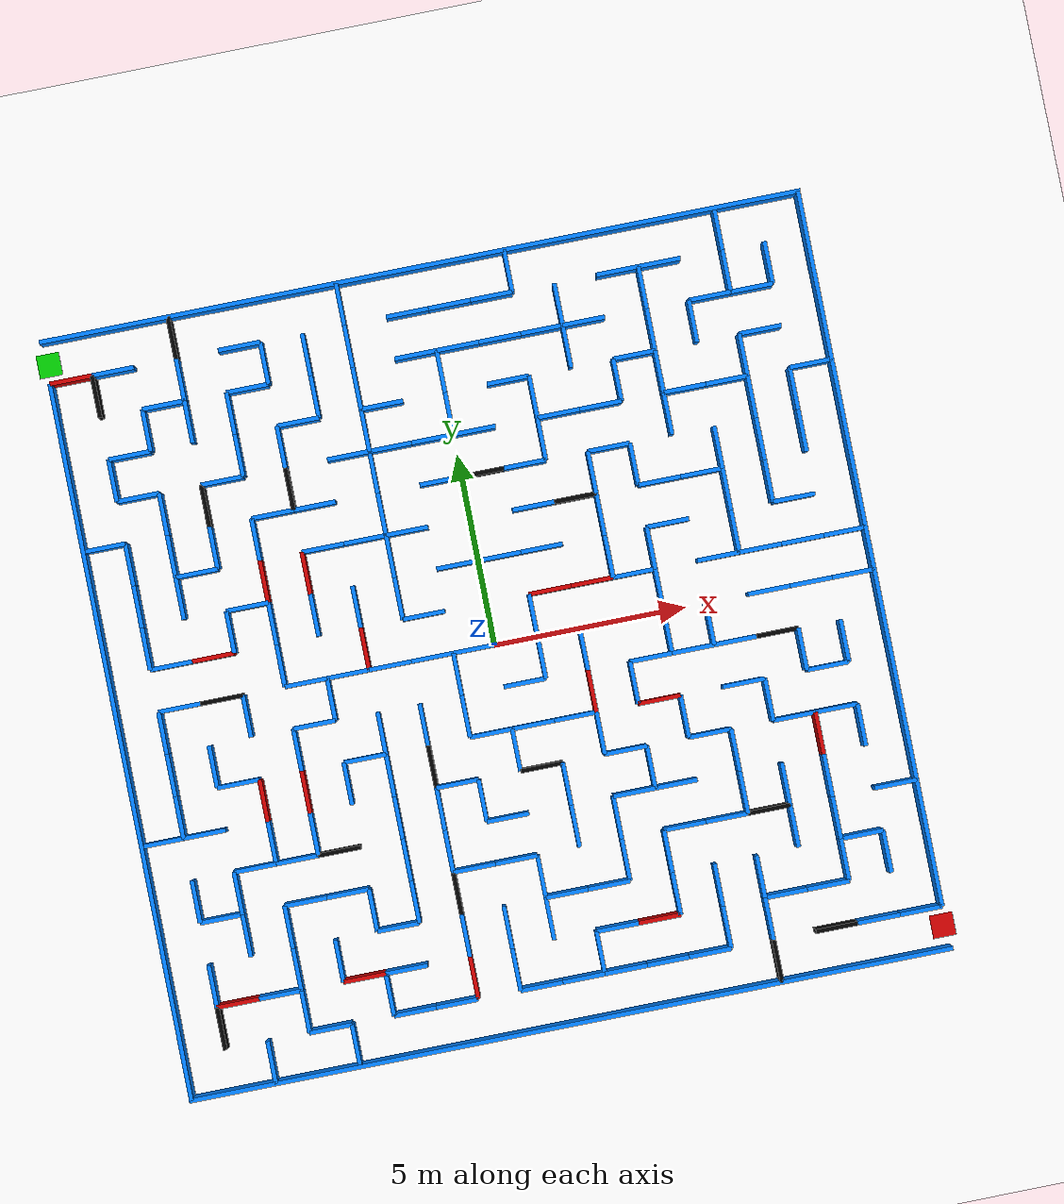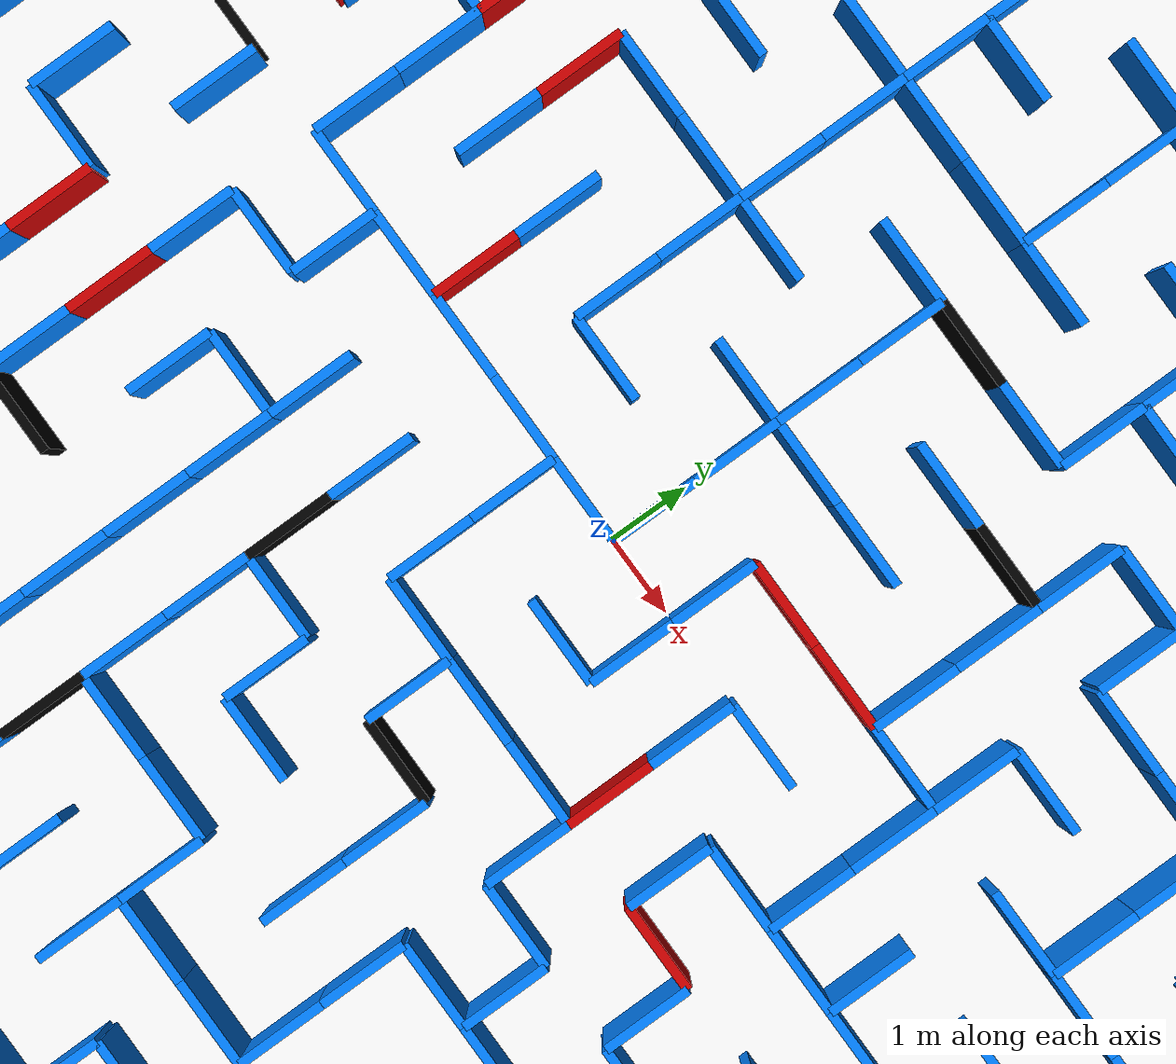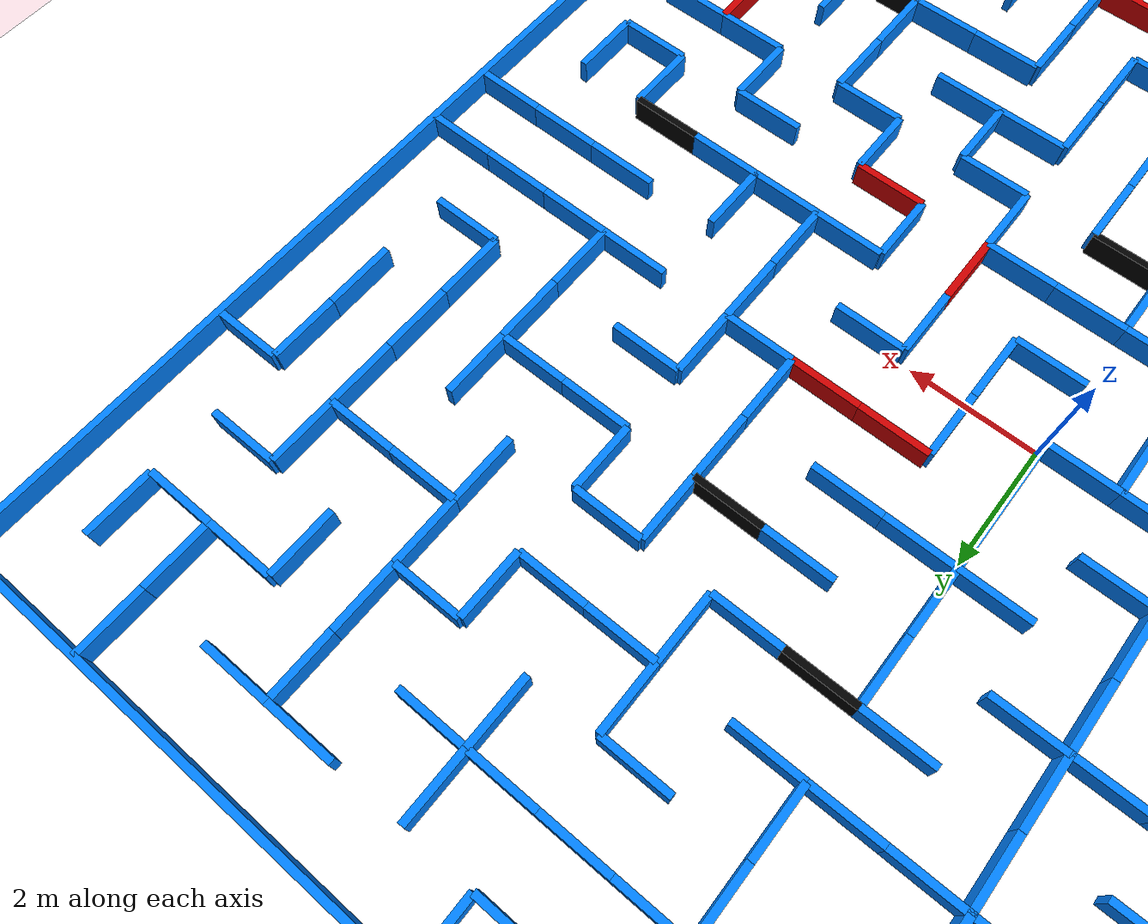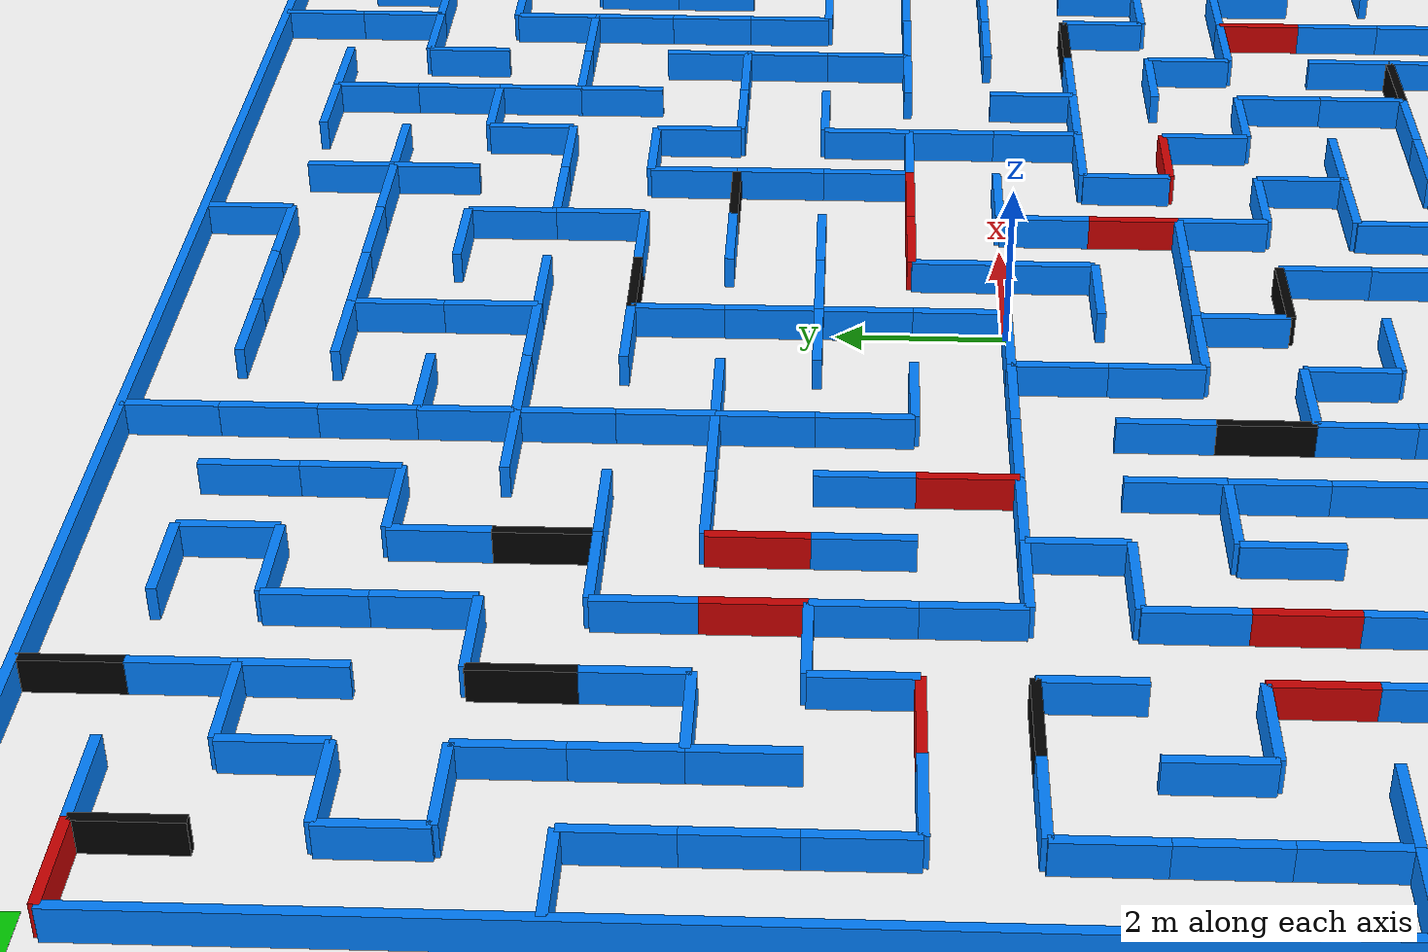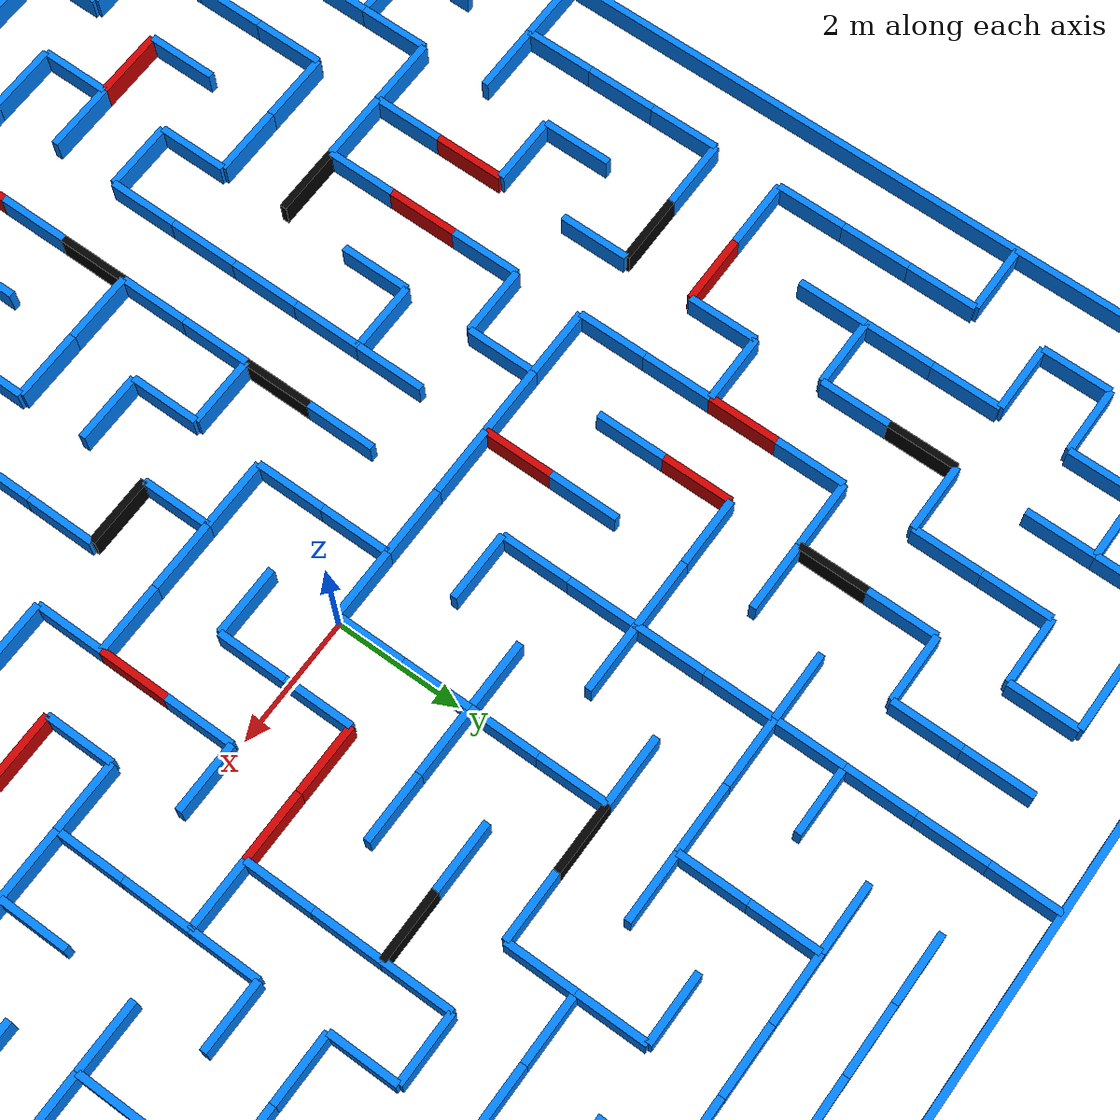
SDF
<?xml version="1.0" ?>
<sdf version="1.6">
  <world name="Hard_Blue_Maze_16x16_braided">

    <light type="directional" name="sun">
      <cast_shadows>true</cast_shadows>
      <pose>0 0 10 0 0 0</pose>
      <diffuse>1.0 1.0 1.0 1</diffuse>
      <specular>0.5 0.5 0.5 1</specular>
      <direction>-0.5 0.2 -0.9</direction>
    </light>

    <model name="ground_plane">
      <static>true</static>
      <link name="link">
        <collision name="collision"><geometry><plane><normal>0 0 1</normal><size>25.8 25.8</size></plane></geometry></collision>
        <visual name="visual">
          <geometry><plane><normal>0 0 1</normal><size>25.8 25.8</size></plane></geometry>
          <material><ambient>1 1 1 1</ambient><diffuse>1 1 1 1</diffuse></material>
        </visual>
      </link>
    </model>

    <!-- เขาวงกต 16x16 + braid loops บางจุด: ทางแยกเยอะ ทางหลอกเยอะ ยากกว่าเดิมมาก -->
    <model name="hard_maze">
      <static>true</static>
      <link name="walls_link">

        <collision name="c_out_top"><pose>0.000 9.900 0.2 0 0 0</pose><geometry><box><size>19.920 0.110 0.400</size></box></geometry></collision>
        <visual name="v_out_top"><pose>0.000 9.900 0.2 0 0 0</pose><geometry><box><size>19.920 0.110 0.400</size></box></geometry><material><ambient>0 0.5 1 1</ambient><diffuse>0 0.5 1 1</diffuse></material></visual>
        <collision name="c_out_bot"><pose>0.000 -9.900 0.2 0 0 0</pose><geometry><box><size>19.920 0.110 0.400</size></box></geometry></collision>
        <visual name="v_out_bot"><pose>0.000 -9.900 0.2 0 0 0</pose><geometry><box><size>19.920 0.110 0.400</size></box></geometry><material><ambient>0 0.5 1 1</ambient><diffuse>0 0.5 1 1</diffuse></material></visual>
        <collision name="c_out_left"><pose>-9.900 -0.550 0.2 0 0 0</pose><geometry><box><size>0.110 18.700 0.400</size></box></geometry></collision>
        <visual name="v_out_left"><pose>-9.900 -0.550 0.2 0 0 0</pose><geometry><box><size>0.110 18.700 0.400</size></box></geometry><material><ambient>0 0.5 1 1</ambient><diffuse>0 0.5 1 1</diffuse></material></visual>
        <collision name="c_out_right"><pose>9.900 0.550 0.2 0 0 0</pose><geometry><box><size>0.110 18.700 0.400</size></box></geometry></collision>
        <visual name="v_out_right"><pose>9.900 0.550 0.2 0 0 0</pose><geometry><box><size>0.110 18.700 0.400</size></box></geometry><material><ambient>0 0.5 1 1</ambient><diffuse>0 0.5 1 1</diffuse></material></visual>
        <collision name="c_v_1_1"><pose>-8.800 8.250 0.2 0 0 0</pose><geometry><box><size>0.110 1.100 0.400</size></box></geometry></collision>
        <visual name="v_v_1_1"><pose>-8.800 8.250 0.2 0 0 0</pose><geometry><box><size>0.110 1.100 0.400</size></box></geometry><material><ambient>0 0 0 1</ambient><diffuse>0 0 0 1</diffuse></material></visual>
        <collision name="c_v_3_1"><pose>-8.800 6.050 0.2 0 0 0</pose><geometry><box><size>0.110 1.100 0.400</size></box></geometry></collision>
        <visual name="v_v_3_1"><pose>-8.800 6.050 0.2 0 0 0</pose><geometry><box><size>0.110 1.100 0.400</size></box></geometry><material><ambient>0 0.5 1 1</ambient><diffuse>0 0.5 1 1</diffuse></material></visual>
        <collision name="c_v_5_1"><pose>-8.800 3.850 0.2 0 0 0</pose><geometry><box><size>0.110 1.100 0.400</size></box></geometry></collision>
        <visual name="v_v_5_1"><pose>-8.800 3.850 0.2 0 0 0</pose><geometry><box><size>0.110 1.100 0.400</size></box></geometry><material><ambient>0 0.5 1 1</ambient><diffuse>0 0.5 1 1</diffuse></material></visual>
        <collision name="c_v_6_1"><pose>-8.800 2.750 0.2 0 0 0</pose><geometry><box><size>0.110 1.100 0.400</size></box></geometry></collision>
        <visual name="v_v_6_1"><pose>-8.800 2.750 0.2 0 0 0</pose><geometry><box><size>0.110 1.100 0.400</size></box></geometry><material><ambient>0 0.5 1 1</ambient><diffuse>0 0.5 1 1</diffuse></material></visual>
        <collision name="c_v_7_1"><pose>-8.800 1.650 0.2 0 0 0</pose><geometry><box><size>0.110 1.100 0.400</size></box></geometry></collision>
        <visual name="v_v_7_1"><pose>-8.800 1.650 0.2 0 0 0</pose><geometry><box><size>0.110 1.100 0.400</size></box></geometry><material><ambient>0 0.5 1 1</ambient><diffuse>0 0.5 1 1</diffuse></material></visual>
        <collision name="c_v_9_1"><pose>-8.800 -0.550 0.2 0 0 0</pose><geometry><box><size>0.110 1.100 0.400</size></box></geometry></collision>
        <visual name="v_v_9_1"><pose>-8.800 -0.550 0.2 0 0 0</pose><geometry><box><size>0.110 1.100 0.400</size></box></geometry><material><ambient>0 0.5 1 1</ambient><diffuse>0 0.5 1 1</diffuse></material></visual>
        <collision name="c_v_10_1"><pose>-8.800 -1.650 0.2 0 0 0</pose><geometry><box><size>0.110 1.100 0.400</size></box></geometry></collision>
        <visual name="v_v_10_1"><pose>-8.800 -1.650 0.2 0 0 0</pose><geometry><box><size>0.110 1.100 0.400</size></box></geometry><material><ambient>0 0.5 1 1</ambient><diffuse>0 0.5 1 1</diffuse></material></visual>
        <collision name="c_v_11_1"><pose>-8.800 -2.750 0.2 0 0 0</pose><geometry><box><size>0.110 1.100 0.400</size></box></geometry></collision>
        <visual name="v_v_11_1"><pose>-8.800 -2.750 0.2 0 0 0</pose><geometry><box><size>0.110 1.100 0.400</size></box></geometry><material><ambient>0 0.5 1 1</ambient><diffuse>0 0.5 1 1</diffuse></material></visual>
        <collision name="c_v_13_1"><pose>-8.800 -4.950 0.2 0 0 0</pose><geometry><box><size>0.110 1.100 0.400</size></box></geometry></collision>
        <visual name="v_v_13_1"><pose>-8.800 -4.950 0.2 0 0 0</pose><geometry><box><size>0.110 1.100 0.400</size></box></geometry><material><ambient>0 0.5 1 1</ambient><diffuse>0 0.5 1 1</diffuse></material></visual>
        <collision name="c_v_15_1"><pose>-8.800 -7.150 0.2 0 0 0</pose><geometry><box><size>0.110 1.100 0.400</size></box></geometry></collision>
        <visual name="v_v_15_1"><pose>-8.800 -7.150 0.2 0 0 0</pose><geometry><box><size>0.110 1.100 0.400</size></box></geometry><material><ambient>0 0.5 1 1</ambient><diffuse>0 0.5 1 1</diffuse></material></visual>
        <collision name="c_v_16_1"><pose>-8.800 -8.250 0.2 0 0 0</pose><geometry><box><size>0.110 1.100 0.400</size></box></geometry></collision>
        <visual name="v_v_16_1"><pose>-8.800 -8.250 0.2 0 0 0</pose><geometry><box><size>0.110 1.100 0.400</size></box></geometry><material><ambient>0 0 0 1</ambient><diffuse>0 0 0 1</diffuse></material></visual>
        <collision name="c_v_2_2"><pose>-7.700 7.150 0.2 0 0 0</pose><geometry><box><size>0.110 1.100 0.400</size></box></geometry></collision>
        <visual name="v_v_2_2"><pose>-7.700 7.150 0.2 0 0 0</pose><geometry><box><size>0.110 1.100 0.400</size></box></geometry><material><ambient>0 0.5 1 1</ambient><diffuse>0 0.5 1 1</diffuse></material></visual>
        <collision name="c_v_4_2"><pose>-7.700 4.950 0.2 0 0 0</pose><geometry><box><size>0.110 1.100 0.400</size></box></geometry></collision>
        <visual name="v_v_4_2"><pose>-7.700 4.950 0.2 0 0 0</pose><geometry><box><size>0.110 1.100 0.400</size></box></geometry><material><ambient>0 0.5 1 1</ambient><diffuse>0 0.5 1 1</diffuse></material></visual>
        <collision name="c_v_5_2"><pose>-7.700 3.850 0.2 0 0 0</pose><geometry><box><size>0.110 1.100 0.400</size></box></geometry></collision>
        <visual name="v_v_5_2"><pose>-7.700 3.850 0.2 0 0 0</pose><geometry><box><size>0.110 1.100 0.400</size></box></geometry><material><ambient>0 0.5 1 1</ambient><diffuse>0 0.5 1 1</diffuse></material></visual>
        <collision name="c_v_6_2"><pose>-7.700 2.750 0.2 0 0 0</pose><geometry><box><size>0.110 1.100 0.400</size></box></geometry></collision>
        <visual name="v_v_6_2"><pose>-7.700 2.750 0.2 0 0 0</pose><geometry><box><size>0.110 1.100 0.400</size></box></geometry><material><ambient>0 0.5 1 1</ambient><diffuse>0 0.5 1 1</diffuse></material></visual>
        <collision name="c_v_10_2"><pose>-7.700 -1.650 0.2 0 0 0</pose><geometry><box><size>0.110 1.100 0.400</size></box></geometry></collision>
        <visual name="v_v_10_2"><pose>-7.700 -1.650 0.2 0 0 0</pose><geometry><box><size>0.110 1.100 0.400</size></box></geometry><material><ambient>0 0.5 1 1</ambient><diffuse>0 0.5 1 1</diffuse></material></visual>
        <collision name="c_v_13_2"><pose>-7.700 -4.950 0.2 0 0 0</pose><geometry><box><size>0.110 1.100 0.400</size></box></geometry></collision>
        <visual name="v_v_13_2"><pose>-7.700 -4.950 0.2 0 0 0</pose><geometry><box><size>0.110 1.100 0.400</size></box></geometry><material><ambient>0 0.5 1 1</ambient><diffuse>0 0.5 1 1</diffuse></material></visual>
        <collision name="c_v_14_2"><pose>-7.700 -6.050 0.2 0 0 0</pose><geometry><box><size>0.110 1.100 0.400</size></box></geometry></collision>
        <visual name="v_v_14_2"><pose>-7.700 -6.050 0.2 0 0 0</pose><geometry><box><size>0.110 1.100 0.400</size></box></geometry><material><ambient>0 0.5 1 1</ambient><diffuse>0 0.5 1 1</diffuse></material></visual>
        <collision name="c_v_17_2"><pose>-7.700 -9.350 0.2 0 0 0</pose><geometry><box><size>0.110 1.100 0.400</size></box></geometry></collision>
        <visual name="v_v_17_2"><pose>-7.700 -9.350 0.2 0 0 0</pose><geometry><box><size>0.110 1.100 0.400</size></box></geometry><material><ambient>0 0.5 1 1</ambient><diffuse>0 0.5 1 1</diffuse></material></visual>
        <collision name="c_v_0_3"><pose>-6.600 9.350 0.2 0 0 0</pose><geometry><box><size>0.110 1.100 0.400</size></box></geometry></collision>
        <visual name="v_v_0_3"><pose>-6.600 9.350 0.2 0 0 0</pose><geometry><box><size>0.110 1.100 0.400</size></box></geometry><material><ambient>0 0 0 1</ambient><diffuse>0 0 0 1</diffuse></material></visual>
        <collision name="c_v_1_3"><pose>-6.600 8.250 0.2 0 0 0</pose><geometry><box><size>0.110 1.100 0.400</size></box></geometry></collision>
        <visual name="v_v_1_3"><pose>-6.600 8.250 0.2 0 0 0</pose><geometry><box><size>0.110 1.100 0.400</size></box></geometry><material><ambient>0 0.5 1 1</ambient><diffuse>0 0.5 1 1</diffuse></material></visual>
        <collision name="c_v_2_3"><pose>-6.600 7.150 0.2 0 0 0</pose><geometry><box><size>0.110 1.100 0.400</size></box></geometry></collision>
        <visual name="v_v_2_3"><pose>-6.600 7.150 0.2 0 0 0</pose><geometry><box><size>0.110 1.100 0.400</size></box></geometry><material><ambient>0 0.5 1 1</ambient><diffuse>0 0.5 1 1</diffuse></material></visual>
        <collision name="c_v_4_3"><pose>-6.600 4.950 0.2 0 0 0</pose><geometry><box><size>0.110 1.100 0.400</size></box></geometry></collision>
        <visual name="v_v_4_3"><pose>-6.600 4.950 0.2 0 0 0</pose><geometry><box><size>0.110 1.100 0.400</size></box></geometry><material><ambient>0 0 0 1</ambient><diffuse>0 0 0 1</diffuse></material></visual>
        <collision name="c_v_5_3"><pose>-6.600 3.850 0.2 0 0 0</pose><geometry><box><size>0.110 1.100 0.400</size></box></geometry></collision>
        <visual name="v_v_5_3"><pose>-6.600 3.850 0.2 0 0 0</pose><geometry><box><size>0.110 1.100 0.400</size></box></geometry><material><ambient>0 0.5 1 1</ambient><diffuse>0 0.5 1 1</diffuse></material></visual>
        <collision name="c_v_7_3"><pose>-6.600 1.650 0.2 0 0 0</pose><geometry><box><size>0.110 1.100 0.400</size></box></geometry></collision>
        <visual name="v_v_7_3"><pose>-6.600 1.650 0.2 0 0 0</pose><geometry><box><size>0.110 1.100 0.400</size></box></geometry><material><ambient>0 0.5 1 1</ambient><diffuse>0 0.5 1 1</diffuse></material></visual>
        <collision name="c_v_9_3"><pose>-6.600 -0.550 0.2 0 0 0</pose><geometry><box><size>0.110 1.100 0.400</size></box></geometry></collision>
        <visual name="v_v_9_3"><pose>-6.600 -0.550 0.2 0 0 0</pose><geometry><box><size>0.110 1.100 0.400</size></box></geometry><material><ambient>0 0.5 1 1</ambient><diffuse>0 0.5 1 1</diffuse></material></visual>
        <collision name="c_v_11_3"><pose>-6.600 -2.750 0.2 0 0 0</pose><geometry><box><size>0.110 1.100 0.400</size></box></geometry></collision>
        <visual name="v_v_11_3"><pose>-6.600 -2.750 0.2 0 0 0</pose><geometry><box><size>0.110 1.100 0.400</size></box></geometry><material><ambient>0.8 0 0 1</ambient><diffuse>0.8 0 0 1</diffuse></material></visual>
        <collision name="c_v_12_3"><pose>-6.600 -3.850 0.2 0 0 0</pose><geometry><box><size>0.110 1.100 0.400</size></box></geometry></collision>
        <visual name="v_v_12_3"><pose>-6.600 -3.850 0.2 0 0 0</pose><geometry><box><size>0.110 1.100 0.400</size></box></geometry><material><ambient>0 0.5 1 1</ambient><diffuse>0 0.5 1 1</diffuse></material></visual>
        <collision name="c_v_14_3"><pose>-6.600 -6.050 0.2 0 0 0</pose><geometry><box><size>0.110 1.100 0.400</size></box></geometry></collision>
        <visual name="v_v_14_3"><pose>-6.600 -6.050 0.2 0 0 0</pose><geometry><box><size>0.110 1.100 0.400</size></box></geometry><material><ambient>0 0.5 1 1</ambient><diffuse>0 0.5 1 1</diffuse></material></visual>
        <collision name="c_v_15_3"><pose>-6.600 -7.150 0.2 0 0 0</pose><geometry><box><size>0.110 1.100 0.400</size></box></geometry></collision>
        <visual name="v_v_15_3"><pose>-6.600 -7.150 0.2 0 0 0</pose><geometry><box><size>0.110 1.100 0.400</size></box></geometry><material><ambient>0 0.5 1 1</ambient><diffuse>0 0.5 1 1</diffuse></material></visual>
        <collision name="c_v_16_3"><pose>-6.600 -8.250 0.2 0 0 0</pose><geometry><box><size>0.110 1.100 0.400</size></box></geometry></collision>
        <visual name="v_v_16_3"><pose>-6.600 -8.250 0.2 0 0 0</pose><geometry><box><size>0.110 1.100 0.400</size></box></geometry><material><ambient>0 0.5 1 1</ambient><diffuse>0 0.5 1 1</diffuse></material></visual>
        <collision name="c_v_2_4"><pose>-5.500 7.150 0.2 0 0 0</pose><geometry><box><size>0.110 1.100 0.400</size></box></geometry></collision>
        <visual name="v_v_2_4"><pose>-5.500 7.150 0.2 0 0 0</pose><geometry><box><size>0.110 1.100 0.400</size></box></geometry><material><ambient>0 0.5 1 1</ambient><diffuse>0 0.5 1 1</diffuse></material></visual>
        <collision name="c_v_3_4"><pose>-5.500 6.050 0.2 0 0 0</pose><geometry><box><size>0.110 1.100 0.400</size></box></geometry></collision>
        <visual name="v_v_3_4"><pose>-5.500 6.050 0.2 0 0 0</pose><geometry><box><size>0.110 1.100 0.400</size></box></geometry><material><ambient>0 0.5 1 1</ambient><diffuse>0 0.5 1 1</diffuse></material></visual>
        <collision name="c_v_5_4"><pose>-5.500 3.850 0.2 0 0 0</pose><geometry><box><size>0.110 1.100 0.400</size></box></geometry></collision>
        <visual name="v_v_5_4"><pose>-5.500 3.850 0.2 0 0 0</pose><geometry><box><size>0.110 1.100 0.400</size></box></geometry><material><ambient>0 0.5 1 1</ambient><diffuse>0 0.5 1 1</diffuse></material></visual>
        <collision name="c_v_6_4"><pose>-5.500 2.750 0.2 0 0 0</pose><geometry><box><size>0.110 1.100 0.400</size></box></geometry></collision>
        <visual name="v_v_6_4"><pose>-5.500 2.750 0.2 0 0 0</pose><geometry><box><size>0.110 1.100 0.400</size></box></geometry><material><ambient>0.8 0 0 1</ambient><diffuse>0.8 0 0 1</diffuse></material></visual>
        <collision name="c_v_7_4"><pose>-5.500 1.650 0.2 0 0 0</pose><geometry><box><size>0.110 1.100 0.400</size></box></geometry></collision>
        <visual name="v_v_7_4"><pose>-5.500 1.650 0.2 0 0 0</pose><geometry><box><size>0.110 1.100 0.400</size></box></geometry><material><ambient>0 0.5 1 1</ambient><diffuse>0 0.5 1 1</diffuse></material></visual>
        <collision name="c_v_8_4"><pose>-5.500 0.550 0.2 0 0 0</pose><geometry><box><size>0.110 1.100 0.400</size></box></geometry></collision>
        <visual name="v_v_8_4"><pose>-5.500 0.550 0.2 0 0 0</pose><geometry><box><size>0.110 1.100 0.400</size></box></geometry><material><ambient>0 0.5 1 1</ambient><diffuse>0 0.5 1 1</diffuse></material></visual>
        <collision name="c_v_10_4"><pose>-5.500 -1.650 0.2 0 0 0</pose><geometry><box><size>0.110 1.100 0.400</size></box></geometry></collision>
        <visual name="v_v_10_4"><pose>-5.500 -1.650 0.2 0 0 0</pose><geometry><box><size>0.110 1.100 0.400</size></box></geometry><material><ambient>0 0.5 1 1</ambient><diffuse>0 0.5 1 1</diffuse></material></visual>
        <collision name="c_v_11_4"><pose>-5.500 -2.750 0.2 0 0 0</pose><geometry><box><size>0.110 1.100 0.400</size></box></geometry></collision>
        <visual name="v_v_11_4"><pose>-5.500 -2.750 0.2 0 0 0</pose><geometry><box><size>0.110 1.100 0.400</size></box></geometry><material><ambient>0.8 0 0 1</ambient><diffuse>0.8 0 0 1</diffuse></material></visual>
        <collision name="c_v_12_4"><pose>-5.500 -3.850 0.2 0 0 0</pose><geometry><box><size>0.110 1.100 0.400</size></box></geometry></collision>
        <visual name="v_v_12_4"><pose>-5.500 -3.850 0.2 0 0 0</pose><geometry><box><size>0.110 1.100 0.400</size></box></geometry><material><ambient>0 0.5 1 1</ambient><diffuse>0 0.5 1 1</diffuse></material></visual>
        <collision name="c_v_15_4"><pose>-5.500 -7.150 0.2 0 0 0</pose><geometry><box><size>0.110 1.100 0.400</size></box></geometry></collision>
        <visual name="v_v_15_4"><pose>-5.500 -7.150 0.2 0 0 0</pose><geometry><box><size>0.110 1.100 0.400</size></box></geometry><material><ambient>0 0.5 1 1</ambient><diffuse>0 0.5 1 1</diffuse></material></visual>
        <collision name="c_v_17_4"><pose>-5.500 -9.350 0.2 0 0 0</pose><geometry><box><size>0.110 1.100 0.400</size></box></geometry></collision>
        <visual name="v_v_17_4"><pose>-5.500 -9.350 0.2 0 0 0</pose><geometry><box><size>0.110 1.100 0.400</size></box></geometry><material><ambient>0 0.5 1 1</ambient><diffuse>0 0.5 1 1</diffuse></material></visual>
        <collision name="c_v_1_5"><pose>-4.400 8.250 0.2 0 0 0</pose><geometry><box><size>0.110 1.100 0.400</size></box></geometry></collision>
        <visual name="v_v_1_5"><pose>-4.400 8.250 0.2 0 0 0</pose><geometry><box><size>0.110 1.100 0.400</size></box></geometry><material><ambient>0 0.5 1 1</ambient><diffuse>0 0.5 1 1</diffuse></material></visual>
        <collision name="c_v_3_5"><pose>-4.400 6.050 0.2 0 0 0</pose><geometry><box><size>0.110 1.100 0.400</size></box></geometry></collision>
        <visual name="v_v_3_5"><pose>-4.400 6.050 0.2 0 0 0</pose><geometry><box><size>0.110 1.100 0.400</size></box></geometry><material><ambient>0 0.5 1 1</ambient><diffuse>0 0.5 1 1</diffuse></material></visual>
        <collision name="c_v_4_5"><pose>-4.400 4.950 0.2 0 0 0</pose><geometry><box><size>0.110 1.100 0.400</size></box></geometry></collision>
        <visual name="v_v_4_5"><pose>-4.400 4.950 0.2 0 0 0</pose><geometry><box><size>0.110 1.100 0.400</size></box></geometry><material><ambient>0 0 0 1</ambient><diffuse>0 0 0 1</diffuse></material></visual>
        <collision name="c_v_6_5"><pose>-4.400 2.750 0.2 0 0 0</pose><geometry><box><size>0.110 1.100 0.400</size></box></geometry></collision>
        <visual name="v_v_6_5"><pose>-4.400 2.750 0.2 0 0 0</pose><geometry><box><size>0.110 1.100 0.400</size></box></geometry><material><ambient>0.8 0 0 1</ambient><diffuse>0.8 0 0 1</diffuse></material></visual>
        <collision name="c_v_7_5"><pose>-4.400 1.650 0.2 0 0 0</pose><geometry><box><size>0.110 1.100 0.400</size></box></geometry></collision>
        <visual name="v_v_7_5"><pose>-4.400 1.650 0.2 0 0 0</pose><geometry><box><size>0.110 1.100 0.400</size></box></geometry><material><ambient>0 0.5 1 1</ambient><diffuse>0 0.5 1 1</diffuse></material></visual>
        <collision name="c_v_9_5"><pose>-4.400 -0.550 0.2 0 0 0</pose><geometry><box><size>0.110 1.100 0.400</size></box></geometry></collision>
        <visual name="v_v_9_5"><pose>-4.400 -0.550 0.2 0 0 0</pose><geometry><box><size>0.110 1.100 0.400</size></box></geometry><material><ambient>0 0.5 1 1</ambient><diffuse>0 0.5 1 1</diffuse></material></visual>
        <collision name="c_v_11_5"><pose>-4.400 -2.750 0.2 0 0 0</pose><geometry><box><size>0.110 1.100 0.400</size></box></geometry></collision>
        <visual name="v_v_11_5"><pose>-4.400 -2.750 0.2 0 0 0</pose><geometry><box><size>0.110 1.100 0.400</size></box></geometry><material><ambient>0 0.5 1 1</ambient><diffuse>0 0.5 1 1</diffuse></material></visual>
        <collision name="c_v_14_5"><pose>-4.400 -6.050 0.2 0 0 0</pose><geometry><box><size>0.110 1.100 0.400</size></box></geometry></collision>
        <visual name="v_v_14_5"><pose>-4.400 -6.050 0.2 0 0 0</pose><geometry><box><size>0.110 1.100 0.400</size></box></geometry><material><ambient>0 0.5 1 1</ambient><diffuse>0 0.5 1 1</diffuse></material></visual>
        <collision name="c_v_16_5"><pose>-4.400 -8.250 0.2 0 0 0</pose><geometry><box><size>0.110 1.100 0.400</size></box></geometry></collision>
        <visual name="v_v_16_5"><pose>-4.400 -8.250 0.2 0 0 0</pose><geometry><box><size>0.110 1.100 0.400</size></box></geometry><material><ambient>0 0.5 1 1</ambient><diffuse>0 0.5 1 1</diffuse></material></visual>
        <collision name="c_v_1_6"><pose>-3.300 8.250 0.2 0 0 0</pose><geometry><box><size>0.110 1.100 0.400</size></box></geometry></collision>
        <visual name="v_v_1_6"><pose>-3.300 8.250 0.2 0 0 0</pose><geometry><box><size>0.110 1.100 0.400</size></box></geometry><material><ambient>0 0.5 1 1</ambient><diffuse>0 0.5 1 1</diffuse></material></visual>
        <collision name="c_v_2_6"><pose>-3.300 7.150 0.2 0 0 0</pose><geometry><box><size>0.110 1.100 0.400</size></box></geometry></collision>
        <visual name="v_v_2_6"><pose>-3.300 7.150 0.2 0 0 0</pose><geometry><box><size>0.110 1.100 0.400</size></box></geometry><material><ambient>0 0.5 1 1</ambient><diffuse>0 0.5 1 1</diffuse></material></visual>
        <collision name="c_v_7_6"><pose>-3.300 1.650 0.2 0 0 0</pose><geometry><box><size>0.110 1.100 0.400</size></box></geometry></collision>
        <visual name="v_v_7_6"><pose>-3.300 1.650 0.2 0 0 0</pose><geometry><box><size>0.110 1.100 0.400</size></box></geometry><material><ambient>0 0.5 1 1</ambient><diffuse>0 0.5 1 1</diffuse></material></visual>
        <collision name="c_v_8_6"><pose>-3.300 0.550 0.2 0 0 0</pose><geometry><box><size>0.110 1.100 0.400</size></box></geometry></collision>
        <visual name="v_v_8_6"><pose>-3.300 0.550 0.2 0 0 0</pose><geometry><box><size>0.110 1.100 0.400</size></box></geometry><material><ambient>0.8 0 0 1</ambient><diffuse>0.8 0 0 1</diffuse></material></visual>
        <collision name="c_v_10_6"><pose>-3.300 -1.650 0.2 0 0 0</pose><geometry><box><size>0.110 1.100 0.400</size></box></geometry></collision>
        <visual name="v_v_10_6"><pose>-3.300 -1.650 0.2 0 0 0</pose><geometry><box><size>0.110 1.100 0.400</size></box></geometry><material><ambient>0 0.5 1 1</ambient><diffuse>0 0.5 1 1</diffuse></material></visual>
        <collision name="c_v_11_6"><pose>-3.300 -2.750 0.2 0 0 0</pose><geometry><box><size>0.110 1.100 0.400</size></box></geometry></collision>
        <visual name="v_v_11_6"><pose>-3.300 -2.750 0.2 0 0 0</pose><geometry><box><size>0.110 1.100 0.400</size></box></geometry><material><ambient>0 0.5 1 1</ambient><diffuse>0 0.5 1 1</diffuse></material></visual>
        <collision name="c_v_12_6"><pose>-3.300 -3.850 0.2 0 0 0</pose><geometry><box><size>0.110 1.100 0.400</size></box></geometry></collision>
        <visual name="v_v_12_6"><pose>-3.300 -3.850 0.2 0 0 0</pose><geometry><box><size>0.110 1.100 0.400</size></box></geometry><material><ambient>0 0.5 1 1</ambient><diffuse>0 0.5 1 1</diffuse></material></visual>
        <collision name="c_v_13_6"><pose>-3.300 -4.950 0.2 0 0 0</pose><geometry><box><size>0.110 1.100 0.400</size></box></geometry></collision>
        <visual name="v_v_13_6"><pose>-3.300 -4.950 0.2 0 0 0</pose><geometry><box><size>0.110 1.100 0.400</size></box></geometry><material><ambient>0 0.5 1 1</ambient><diffuse>0 0.5 1 1</diffuse></material></visual>
        <collision name="c_v_14_6"><pose>-3.300 -6.050 0.2 0 0 0</pose><geometry><box><size>0.110 1.100 0.400</size></box></geometry></collision>
        <visual name="v_v_14_6"><pose>-3.300 -6.050 0.2 0 0 0</pose><geometry><box><size>0.110 1.100 0.400</size></box></geometry><material><ambient>0 0.5 1 1</ambient><diffuse>0 0.5 1 1</diffuse></material></visual>
        <collision name="c_v_0_7"><pose>-2.200 9.350 0.2 0 0 0</pose><geometry><box><size>0.110 1.100 0.400</size></box></geometry></collision>
        <visual name="v_v_0_7"><pose>-2.200 9.350 0.2 0 0 0</pose><geometry><box><size>0.110 1.100 0.400</size></box></geometry><material><ambient>0 0.5 1 1</ambient><diffuse>0 0.5 1 1</diffuse></material></visual>
        <collision name="c_v_1_7"><pose>-2.200 8.250 0.2 0 0 0</pose><geometry><box><size>0.110 1.100 0.400</size></box></geometry></collision>
        <visual name="v_v_1_7"><pose>-2.200 8.250 0.2 0 0 0</pose><geometry><box><size>0.110 1.100 0.400</size></box></geometry><material><ambient>0 0.5 1 1</ambient><diffuse>0 0.5 1 1</diffuse></material></visual>
        <collision name="c_v_2_7"><pose>-2.200 7.150 0.2 0 0 0</pose><geometry><box><size>0.110 1.100 0.400</size></box></geometry></collision>
        <visual name="v_v_2_7"><pose>-2.200 7.150 0.2 0 0 0</pose><geometry><box><size>0.110 1.100 0.400</size></box></geometry><material><ambient>0 0.5 1 1</ambient><diffuse>0 0.5 1 1</diffuse></material></visual>
        <collision name="c_v_3_7"><pose>-2.200 6.050 0.2 0 0 0</pose><geometry><box><size>0.110 1.100 0.400</size></box></geometry></collision>
        <visual name="v_v_3_7"><pose>-2.200 6.050 0.2 0 0 0</pose><geometry><box><size>0.110 1.100 0.400</size></box></geometry><material><ambient>0 0.5 1 1</ambient><diffuse>0 0.5 1 1</diffuse></material></visual>
        <collision name="c_v_4_7"><pose>-2.200 4.950 0.2 0 0 0</pose><geometry><box><size>0.110 1.100 0.400</size></box></geometry></collision>
        <visual name="v_v_4_7"><pose>-2.200 4.950 0.2 0 0 0</pose><geometry><box><size>0.110 1.100 0.400</size></box></geometry><material><ambient>0 0.5 1 1</ambient><diffuse>0 0.5 1 1</diffuse></material></visual>
        <collision name="c_v_5_7"><pose>-2.200 3.850 0.2 0 0 0</pose><geometry><box><size>0.110 1.100 0.400</size></box></geometry></collision>
        <visual name="v_v_5_7"><pose>-2.200 3.850 0.2 0 0 0</pose><geometry><box><size>0.110 1.100 0.400</size></box></geometry><material><ambient>0 0.5 1 1</ambient><diffuse>0 0.5 1 1</diffuse></material></visual>
        <collision name="c_v_6_7"><pose>-2.200 2.750 0.2 0 0 0</pose><geometry><box><size>0.110 1.100 0.400</size></box></geometry></collision>
        <visual name="v_v_6_7"><pose>-2.200 2.750 0.2 0 0 0</pose><geometry><box><size>0.110 1.100 0.400</size></box></geometry><material><ambient>0 0.5 1 1</ambient><diffuse>0 0.5 1 1</diffuse></material></visual>
        <collision name="c_v_7_7"><pose>-2.200 1.650 0.2 0 0 0</pose><geometry><box><size>0.110 1.100 0.400</size></box></geometry></collision>
        <visual name="v_v_7_7"><pose>-2.200 1.650 0.2 0 0 0</pose><geometry><box><size>0.110 1.100 0.400</size></box></geometry><material><ambient>0 0.5 1 1</ambient><diffuse>0 0.5 1 1</diffuse></material></visual>
        <collision name="c_v_10_7"><pose>-2.200 -1.650 0.2 0 0 0</pose><geometry><box><size>0.110 1.100 0.400</size></box></geometry></collision>
        <visual name="v_v_10_7"><pose>-2.200 -1.650 0.2 0 0 0</pose><geometry><box><size>0.110 1.100 0.400</size></box></geometry><material><ambient>0 0.5 1 1</ambient><diffuse>0 0.5 1 1</diffuse></material></visual>
        <collision name="c_v_11_7"><pose>-2.200 -2.750 0.2 0 0 0</pose><geometry><box><size>0.110 1.100 0.400</size></box></geometry></collision>
        <visual name="v_v_11_7"><pose>-2.200 -2.750 0.2 0 0 0</pose><geometry><box><size>0.110 1.100 0.400</size></box></geometry><material><ambient>0 0 0 1</ambient><diffuse>0 0 0 1</diffuse></material></visual>
        <collision name="c_v_12_7"><pose>-2.200 -3.850 0.2 0 0 0</pose><geometry><box><size>0.110 1.100 0.400</size></box></geometry></collision>
        <visual name="v_v_12_7"><pose>-2.200 -3.850 0.2 0 0 0</pose><geometry><box><size>0.110 1.100 0.400</size></box></geometry><material><ambient>0 0.5 1 1</ambient><diffuse>0 0.5 1 1</diffuse></material></visual>
        <collision name="c_v_13_7"><pose>-2.200 -4.950 0.2 0 0 0</pose><geometry><box><size>0.110 1.100 0.400</size></box></geometry></collision>
        <visual name="v_v_13_7"><pose>-2.200 -4.950 0.2 0 0 0</pose><geometry><box><size>0.110 1.100 0.400</size></box></geometry><material><ambient>0 0.5 1 1</ambient><diffuse>0 0.5 1 1</diffuse></material></visual>
        <collision name="c_v_14_7"><pose>-2.200 -6.050 0.2 0 0 0</pose><geometry><box><size>0.110 1.100 0.400</size></box></geometry></collision>
        <visual name="v_v_14_7"><pose>-2.200 -6.050 0.2 0 0 0</pose><geometry><box><size>0.110 1.100 0.400</size></box></geometry><material><ambient>0 0 0 1</ambient><diffuse>0 0 0 1</diffuse></material></visual>
        <collision name="c_v_15_7"><pose>-2.200 -7.150 0.2 0 0 0</pose><geometry><box><size>0.110 1.100 0.400</size></box></geometry></collision>
        <visual name="v_v_15_7"><pose>-2.200 -7.150 0.2 0 0 0</pose><geometry><box><size>0.110 1.100 0.400</size></box></geometry><material><ambient>0 0.5 1 1</ambient><diffuse>0 0.5 1 1</diffuse></material></visual>
        <collision name="c_v_16_7"><pose>-2.200 -8.250 0.2 0 0 0</pose><geometry><box><size>0.110 1.100 0.400</size></box></geometry></collision>
        <visual name="v_v_16_7"><pose>-2.200 -8.250 0.2 0 0 0</pose><geometry><box><size>0.110 1.100 0.400</size></box></geometry><material><ambient>0.8 0 0 1</ambient><diffuse>0.8 0 0 1</diffuse></material></visual>
        <collision name="c_v_9_8"><pose>-1.100 -0.550 0.2 0 0 0</pose><geometry><box><size>0.110 1.100 0.400</size></box></geometry></collision>
        <visual name="v_v_9_8"><pose>-1.100 -0.550 0.2 0 0 0</pose><geometry><box><size>0.110 1.100 0.400</size></box></geometry><material><ambient>0 0.5 1 1</ambient><diffuse>0 0.5 1 1</diffuse></material></visual>
        <collision name="c_v_10_8"><pose>-1.100 -1.650 0.2 0 0 0</pose><geometry><box><size>0.110 1.100 0.400</size></box></geometry></collision>
        <visual name="v_v_10_8"><pose>-1.100 -1.650 0.2 0 0 0</pose><geometry><box><size>0.110 1.100 0.400</size></box></geometry><material><ambient>0 0.5 1 1</ambient><diffuse>0 0.5 1 1</diffuse></material></visual>
        <collision name="c_v_12_8"><pose>-1.100 -3.850 0.2 0 0 0</pose><geometry><box><size>0.110 1.100 0.400</size></box></geometry></collision>
        <visual name="v_v_12_8"><pose>-1.100 -3.850 0.2 0 0 0</pose><geometry><box><size>0.110 1.100 0.400</size></box></geometry><material><ambient>0 0.5 1 1</ambient><diffuse>0 0.5 1 1</diffuse></material></visual>
        <collision name="c_v_15_8"><pose>-1.100 -7.150 0.2 0 0 0</pose><geometry><box><size>0.110 1.100 0.400</size></box></geometry></collision>
        <visual name="v_v_15_8"><pose>-1.100 -7.150 0.2 0 0 0</pose><geometry><box><size>0.110 1.100 0.400</size></box></geometry><material><ambient>0 0.5 1 1</ambient><diffuse>0 0.5 1 1</diffuse></material></visual>
        <collision name="c_v_16_8"><pose>-1.100 -8.250 0.2 0 0 0</pose><geometry><box><size>0.110 1.100 0.400</size></box></geometry></collision>
        <visual name="v_v_16_8"><pose>-1.100 -8.250 0.2 0 0 0</pose><geometry><box><size>0.110 1.100 0.400</size></box></geometry><material><ambient>0 0.5 1 1</ambient><diffuse>0 0.5 1 1</diffuse></material></visual>
        <collision name="c_v_2_9"><pose>0.000 7.150 0.2 0 0 0</pose><geometry><box><size>0.110 1.100 0.400</size></box></geometry></collision>
        <visual name="v_v_2_9"><pose>0.000 7.150 0.2 0 0 0</pose><geometry><box><size>0.110 1.100 0.400</size></box></geometry><material><ambient>0 0.5 1 1</ambient><diffuse>0 0.5 1 1</diffuse></material></visual>
        <collision name="c_v_3_9"><pose>0.000 6.050 0.2 0 0 0</pose><geometry><box><size>0.110 1.100 0.400</size></box></geometry></collision>
        <visual name="v_v_3_9"><pose>0.000 6.050 0.2 0 0 0</pose><geometry><box><size>0.110 1.100 0.400</size></box></geometry><material><ambient>0 0.5 1 1</ambient><diffuse>0 0.5 1 1</diffuse></material></visual>
        <collision name="c_v_5_9"><pose>0.000 3.850 0.2 0 0 0</pose><geometry><box><size>0.110 1.100 0.400</size></box></geometry></collision>
        <visual name="v_v_5_9"><pose>0.000 3.850 0.2 0 0 0</pose><geometry><box><size>0.110 1.100 0.400</size></box></geometry><material><ambient>0 0.5 1 1</ambient><diffuse>0 0.5 1 1</diffuse></material></visual>
        <collision name="c_v_6_9"><pose>0.000 2.750 0.2 0 0 0</pose><geometry><box><size>0.110 1.100 0.400</size></box></geometry></collision>
        <visual name="v_v_6_9"><pose>0.000 2.750 0.2 0 0 0</pose><geometry><box><size>0.110 1.100 0.400</size></box></geometry><material><ambient>0 0.5 1 1</ambient><diffuse>0 0.5 1 1</diffuse></material></visual>
        <collision name="c_v_7_9"><pose>0.000 1.650 0.2 0 0 0</pose><geometry><box><size>0.110 1.100 0.400</size></box></geometry></collision>
        <visual name="v_v_7_9"><pose>0.000 1.650 0.2 0 0 0</pose><geometry><box><size>0.110 1.100 0.400</size></box></geometry><material><ambient>0 0.5 1 1</ambient><diffuse>0 0.5 1 1</diffuse></material></visual>
        <collision name="c_v_8_9"><pose>0.000 0.550 0.2 0 0 0</pose><geometry><box><size>0.110 1.100 0.400</size></box></geometry></collision>
        <visual name="v_v_8_9"><pose>0.000 0.550 0.2 0 0 0</pose><geometry><box><size>0.110 1.100 0.400</size></box></geometry><material><ambient>0 0.5 1 1</ambient><diffuse>0 0.5 1 1</diffuse></material></visual>
        <collision name="c_v_11_9"><pose>0.000 -2.750 0.2 0 0 0</pose><geometry><box><size>0.110 1.100 0.400</size></box></geometry></collision>
        <visual name="v_v_11_9"><pose>0.000 -2.750 0.2 0 0 0</pose><geometry><box><size>0.110 1.100 0.400</size></box></geometry><material><ambient>0 0.5 1 1</ambient><diffuse>0 0.5 1 1</diffuse></material></visual>
        <collision name="c_v_14_9"><pose>0.000 -6.050 0.2 0 0 0</pose><geometry><box><size>0.110 1.100 0.400</size></box></geometry></collision>
        <visual name="v_v_14_9"><pose>0.000 -6.050 0.2 0 0 0</pose><geometry><box><size>0.110 1.100 0.400</size></box></geometry><material><ambient>0 0.5 1 1</ambient><diffuse>0 0.5 1 1</diffuse></material></visual>
        <collision name="c_v_15_9"><pose>0.000 -7.150 0.2 0 0 0</pose><geometry><box><size>0.110 1.100 0.400</size></box></geometry></collision>
        <visual name="v_v_15_9"><pose>0.000 -7.150 0.2 0 0 0</pose><geometry><box><size>0.110 1.100 0.400</size></box></geometry><material><ambient>0 0.5 1 1</ambient><diffuse>0 0.5 1 1</diffuse></material></visual>
        <collision name="c_v_8_10"><pose>1.100 0.550 0.2 0 0 0</pose><geometry><box><size>0.110 1.100 0.400</size></box></geometry></collision>
        <visual name="v_v_8_10"><pose>1.100 0.550 0.2 0 0 0</pose><geometry><box><size>0.110 1.100 0.400</size></box></geometry><material><ambient>0 0.5 1 1</ambient><diffuse>0 0.5 1 1</diffuse></material></visual>
        <collision name="c_v_9_10"><pose>1.100 -0.550 0.2 0 0 0</pose><geometry><box><size>0.110 1.100 0.400</size></box></geometry></collision>
        <visual name="v_v_9_10"><pose>1.100 -0.550 0.2 0 0 0</pose><geometry><box><size>0.110 1.100 0.400</size></box></geometry><material><ambient>0 0.5 1 1</ambient><diffuse>0 0.5 1 1</diffuse></material></visual>
        <collision name="c_v_12_10"><pose>1.100 -3.850 0.2 0 0 0</pose><geometry><box><size>0.110 1.100 0.400</size></box></geometry></collision>
        <visual name="v_v_12_10"><pose>1.100 -3.850 0.2 0 0 0</pose><geometry><box><size>0.110 1.100 0.400</size></box></geometry><material><ambient>0 0.5 1 1</ambient><diffuse>0 0.5 1 1</diffuse></material></visual>
        <collision name="c_v_13_10"><pose>1.100 -4.950 0.2 0 0 0</pose><geometry><box><size>0.110 1.100 0.400</size></box></geometry></collision>
        <visual name="v_v_13_10"><pose>1.100 -4.950 0.2 0 0 0</pose><geometry><box><size>0.110 1.100 0.400</size></box></geometry><material><ambient>0 0.5 1 1</ambient><diffuse>0 0.5 1 1</diffuse></material></visual>
        <collision name="c_v_16_10"><pose>1.100 -8.250 0.2 0 0 0</pose><geometry><box><size>0.110 1.100 0.400</size></box></geometry></collision>
        <visual name="v_v_16_10"><pose>1.100 -8.250 0.2 0 0 0</pose><geometry><box><size>0.110 1.100 0.400</size></box></geometry><material><ambient>0 0.5 1 1</ambient><diffuse>0 0.5 1 1</diffuse></material></visual>
        <collision name="c_v_0_11"><pose>2.200 9.350 0.2 0 0 0</pose><geometry><box><size>0.110 1.100 0.400</size></box></geometry></collision>
        <visual name="v_v_0_11"><pose>2.200 9.350 0.2 0 0 0</pose><geometry><box><size>0.110 1.100 0.400</size></box></geometry><material><ambient>0 0.5 1 1</ambient><diffuse>0 0.5 1 1</diffuse></material></visual>
        <collision name="c_v_3_11"><pose>2.200 6.050 0.2 0 0 0</pose><geometry><box><size>0.110 1.100 0.400</size></box></geometry></collision>
        <visual name="v_v_3_11"><pose>2.200 6.050 0.2 0 0 0</pose><geometry><box><size>0.110 1.100 0.400</size></box></geometry><material><ambient>0 0.5 1 1</ambient><diffuse>0 0.5 1 1</diffuse></material></visual>
        <collision name="c_v_4_11"><pose>2.200 4.950 0.2 0 0 0</pose><geometry><box><size>0.110 1.100 0.400</size></box></geometry></collision>
        <visual name="v_v_4_11"><pose>2.200 4.950 0.2 0 0 0</pose><geometry><box><size>0.110 1.100 0.400</size></box></geometry><material><ambient>0 0.5 1 1</ambient><diffuse>0 0.5 1 1</diffuse></material></visual>
        <collision name="c_v_9_11"><pose>2.200 -0.550 0.2 0 0 0</pose><geometry><box><size>0.110 1.100 0.400</size></box></geometry></collision>
        <visual name="v_v_9_11"><pose>2.200 -0.550 0.2 0 0 0</pose><geometry><box><size>0.110 1.100 0.400</size></box></geometry><material><ambient>0 0.5 1 1</ambient><diffuse>0 0.5 1 1</diffuse></material></visual>
        <collision name="c_v_10_11"><pose>2.200 -1.650 0.2 0 0 0</pose><geometry><box><size>0.110 1.100 0.400</size></box></geometry></collision>
        <visual name="v_v_10_11"><pose>2.200 -1.650 0.2 0 0 0</pose><geometry><box><size>0.110 1.100 0.400</size></box></geometry><material><ambient>0.8 0 0 1</ambient><diffuse>0.8 0 0 1</diffuse></material></visual>
        <collision name="c_v_11_11"><pose>2.200 -2.750 0.2 0 0 0</pose><geometry><box><size>0.110 1.100 0.400</size></box></geometry></collision>
        <visual name="v_v_11_11"><pose>2.200 -2.750 0.2 0 0 0</pose><geometry><box><size>0.110 1.100 0.400</size></box></geometry><material><ambient>0 0.5 1 1</ambient><diffuse>0 0.5 1 1</diffuse></material></visual>
        <collision name="c_v_13_11"><pose>2.200 -4.950 0.2 0 0 0</pose><geometry><box><size>0.110 1.100 0.400</size></box></geometry></collision>
        <visual name="v_v_13_11"><pose>2.200 -4.950 0.2 0 0 0</pose><geometry><box><size>0.110 1.100 0.400</size></box></geometry><material><ambient>0 0.5 1 1</ambient><diffuse>0 0.5 1 1</diffuse></material></visual>
        <collision name="c_v_14_11"><pose>2.200 -6.050 0.2 0 0 0</pose><geometry><box><size>0.110 1.100 0.400</size></box></geometry></collision>
        <visual name="v_v_14_11"><pose>2.200 -6.050 0.2 0 0 0</pose><geometry><box><size>0.110 1.100 0.400</size></box></geometry><material><ambient>0 0.5 1 1</ambient><diffuse>0 0.5 1 1</diffuse></material></visual>
        <collision name="c_v_1_12"><pose>3.300 8.250 0.2 0 0 0</pose><geometry><box><size>0.110 1.100 0.400</size></box></geometry></collision>
        <visual name="v_v_1_12"><pose>3.300 8.250 0.2 0 0 0</pose><geometry><box><size>0.110 1.100 0.400</size></box></geometry><material><ambient>0 0.5 1 1</ambient><diffuse>0 0.5 1 1</diffuse></material></visual>
        <collision name="c_v_2_12"><pose>3.300 7.150 0.2 0 0 0</pose><geometry><box><size>0.110 1.100 0.400</size></box></geometry></collision>
        <visual name="v_v_2_12"><pose>3.300 7.150 0.2 0 0 0</pose><geometry><box><size>0.110 1.100 0.400</size></box></geometry><material><ambient>0 0.5 1 1</ambient><diffuse>0 0.5 1 1</diffuse></material></visual>
        <collision name="c_v_5_12"><pose>3.300 3.850 0.2 0 0 0</pose><geometry><box><size>0.110 1.100 0.400</size></box></geometry></collision>
        <visual name="v_v_5_12"><pose>3.300 3.850 0.2 0 0 0</pose><geometry><box><size>0.110 1.100 0.400</size></box></geometry><material><ambient>0 0.5 1 1</ambient><diffuse>0 0.5 1 1</diffuse></material></visual>
        <collision name="c_v_6_12"><pose>3.300 2.750 0.2 0 0 0</pose><geometry><box><size>0.110 1.100 0.400</size></box></geometry></collision>
        <visual name="v_v_6_12"><pose>3.300 2.750 0.2 0 0 0</pose><geometry><box><size>0.110 1.100 0.400</size></box></geometry><material><ambient>0 0.5 1 1</ambient><diffuse>0 0.5 1 1</diffuse></material></visual>
        <collision name="c_v_7_12"><pose>3.300 1.650 0.2 0 0 0</pose><geometry><box><size>0.110 1.100 0.400</size></box></geometry></collision>
        <visual name="v_v_7_12"><pose>3.300 1.650 0.2 0 0 0</pose><geometry><box><size>0.110 1.100 0.400</size></box></geometry><material><ambient>0 0.5 1 1</ambient><diffuse>0 0.5 1 1</diffuse></material></visual>
        <collision name="c_v_10_12"><pose>3.300 -1.650 0.2 0 0 0</pose><geometry><box><size>0.110 1.100 0.400</size></box></geometry></collision>
        <visual name="v_v_10_12"><pose>3.300 -1.650 0.2 0 0 0</pose><geometry><box><size>0.110 1.100 0.400</size></box></geometry><material><ambient>0 0.5 1 1</ambient><diffuse>0 0.5 1 1</diffuse></material></visual>
        <collision name="c_v_12_12"><pose>3.300 -3.850 0.2 0 0 0</pose><geometry><box><size>0.110 1.100 0.400</size></box></geometry></collision>
        <visual name="v_v_12_12"><pose>3.300 -3.850 0.2 0 0 0</pose><geometry><box><size>0.110 1.100 0.400</size></box></geometry><material><ambient>0 0.5 1 1</ambient><diffuse>0 0.5 1 1</diffuse></material></visual>
        <collision name="c_v_14_12"><pose>3.300 -6.050 0.2 0 0 0</pose><geometry><box><size>0.110 1.100 0.400</size></box></geometry></collision>
        <visual name="v_v_14_12"><pose>3.300 -6.050 0.2 0 0 0</pose><geometry><box><size>0.110 1.100 0.400</size></box></geometry><material><ambient>0 0.5 1 1</ambient><diffuse>0 0.5 1 1</diffuse></material></visual>
        <collision name="c_v_15_12"><pose>3.300 -7.150 0.2 0 0 0</pose><geometry><box><size>0.110 1.100 0.400</size></box></geometry></collision>
        <visual name="v_v_15_12"><pose>3.300 -7.150 0.2 0 0 0</pose><geometry><box><size>0.110 1.100 0.400</size></box></geometry><material><ambient>0 0.5 1 1</ambient><diffuse>0 0.5 1 1</diffuse></material></visual>
        <collision name="c_v_3_13"><pose>4.400 6.050 0.2 0 0 0</pose><geometry><box><size>0.110 1.100 0.400</size></box></geometry></collision>
        <visual name="v_v_3_13"><pose>4.400 6.050 0.2 0 0 0</pose><geometry><box><size>0.110 1.100 0.400</size></box></geometry><material><ambient>0 0.5 1 1</ambient><diffuse>0 0.5 1 1</diffuse></material></visual>
        <collision name="c_v_5_13"><pose>4.400 3.850 0.2 0 0 0</pose><geometry><box><size>0.110 1.100 0.400</size></box></geometry></collision>
        <visual name="v_v_5_13"><pose>4.400 3.850 0.2 0 0 0</pose><geometry><box><size>0.110 1.100 0.400</size></box></geometry><material><ambient>0 0.5 1 1</ambient><diffuse>0 0.5 1 1</diffuse></material></visual>
        <collision name="c_v_7_13"><pose>4.400 1.650 0.2 0 0 0</pose><geometry><box><size>0.110 1.100 0.400</size></box></geometry></collision>
        <visual name="v_v_7_13"><pose>4.400 1.650 0.2 0 0 0</pose><geometry><box><size>0.110 1.100 0.400</size></box></geometry><material><ambient>0 0.5 1 1</ambient><diffuse>0 0.5 1 1</diffuse></material></visual>
        <collision name="c_v_8_13"><pose>4.400 0.550 0.2 0 0 0</pose><geometry><box><size>0.110 1.100 0.400</size></box></geometry></collision>
        <visual name="v_v_8_13"><pose>4.400 0.550 0.2 0 0 0</pose><geometry><box><size>0.110 1.100 0.400</size></box></geometry><material><ambient>0 0.5 1 1</ambient><diffuse>0 0.5 1 1</diffuse></material></visual>
        <collision name="c_v_9_13"><pose>4.400 -0.550 0.2 0 0 0</pose><geometry><box><size>0.110 1.100 0.400</size></box></geometry></collision>
        <visual name="v_v_9_13"><pose>4.400 -0.550 0.2 0 0 0</pose><geometry><box><size>0.110 1.100 0.400</size></box></geometry><material><ambient>0 0.5 1 1</ambient><diffuse>0 0.5 1 1</diffuse></material></visual>
        <collision name="c_v_11_13"><pose>4.400 -2.750 0.2 0 0 0</pose><geometry><box><size>0.110 1.100 0.400</size></box></geometry></collision>
        <visual name="v_v_11_13"><pose>4.400 -2.750 0.2 0 0 0</pose><geometry><box><size>0.110 1.100 0.400</size></box></geometry><material><ambient>0 0.5 1 1</ambient><diffuse>0 0.5 1 1</diffuse></material></visual>
        <collision name="c_v_15_13"><pose>4.400 -7.150 0.2 0 0 0</pose><geometry><box><size>0.110 1.100 0.400</size></box></geometry></collision>
        <visual name="v_v_15_13"><pose>4.400 -7.150 0.2 0 0 0</pose><geometry><box><size>0.110 1.100 0.400</size></box></geometry><material><ambient>0 0.5 1 1</ambient><diffuse>0 0.5 1 1</diffuse></material></visual>
        <collision name="c_v_16_13"><pose>4.400 -8.250 0.2 0 0 0</pose><geometry><box><size>0.110 1.100 0.400</size></box></geometry></collision>
        <visual name="v_v_16_13"><pose>4.400 -8.250 0.2 0 0 0</pose><geometry><box><size>0.110 1.100 0.400</size></box></geometry><material><ambient>0 0.5 1 1</ambient><diffuse>0 0.5 1 1</diffuse></material></visual>
        <collision name="c_v_1_14"><pose>5.500 8.250 0.2 0 0 0</pose><geometry><box><size>0.110 1.100 0.400</size></box></geometry></collision>
        <visual name="v_v_1_14"><pose>5.500 8.250 0.2 0 0 0</pose><geometry><box><size>0.110 1.100 0.400</size></box></geometry><material><ambient>0 0.5 1 1</ambient><diffuse>0 0.5 1 1</diffuse></material></visual>
        <collision name="c_v_2_14"><pose>5.500 7.150 0.2 0 0 0</pose><geometry><box><size>0.110 1.100 0.400</size></box></geometry></collision>
        <visual name="v_v_2_14"><pose>5.500 7.150 0.2 0 0 0</pose><geometry><box><size>0.110 1.100 0.400</size></box></geometry><material><ambient>0 0.5 1 1</ambient><diffuse>0 0.5 1 1</diffuse></material></visual>
        <collision name="c_v_3_14"><pose>5.500 6.050 0.2 0 0 0</pose><geometry><box><size>0.110 1.100 0.400</size></box></geometry></collision>
        <visual name="v_v_3_14"><pose>5.500 6.050 0.2 0 0 0</pose><geometry><box><size>0.110 1.100 0.400</size></box></geometry><material><ambient>0 0.5 1 1</ambient><diffuse>0 0.5 1 1</diffuse></material></visual>
        <collision name="c_v_4_14"><pose>5.500 4.950 0.2 0 0 0</pose><geometry><box><size>0.110 1.100 0.400</size></box></geometry></collision>
        <visual name="v_v_4_14"><pose>5.500 4.950 0.2 0 0 0</pose><geometry><box><size>0.110 1.100 0.400</size></box></geometry><material><ambient>0 0.5 1 1</ambient><diffuse>0 0.5 1 1</diffuse></material></visual>
        <collision name="c_v_9_14"><pose>5.500 -0.550 0.2 0 0 0</pose><geometry><box><size>0.110 1.100 0.400</size></box></geometry></collision>
        <visual name="v_v_9_14"><pose>5.500 -0.550 0.2 0 0 0</pose><geometry><box><size>0.110 1.100 0.400</size></box></geometry><material><ambient>0 0.5 1 1</ambient><diffuse>0 0.5 1 1</diffuse></material></visual>
        <collision name="c_v_12_14"><pose>5.500 -3.850 0.2 0 0 0</pose><geometry><box><size>0.110 1.100 0.400</size></box></geometry></collision>
        <visual name="v_v_12_14"><pose>5.500 -3.850 0.2 0 0 0</pose><geometry><box><size>0.110 1.100 0.400</size></box></geometry><material><ambient>0 0.5 1 1</ambient><diffuse>0 0.5 1 1</diffuse></material></visual>
        <collision name="c_v_13_14"><pose>5.500 -4.950 0.2 0 0 0</pose><geometry><box><size>0.110 1.100 0.400</size></box></geometry></collision>
        <visual name="v_v_13_14"><pose>5.500 -4.950 0.2 0 0 0</pose><geometry><box><size>0.110 1.100 0.400</size></box></geometry><material><ambient>0 0.5 1 1</ambient><diffuse>0 0.5 1 1</diffuse></material></visual>
        <collision name="c_v_15_14"><pose>5.500 -7.150 0.2 0 0 0</pose><geometry><box><size>0.110 1.100 0.400</size></box></geometry></collision>
        <visual name="v_v_15_14"><pose>5.500 -7.150 0.2 0 0 0</pose><geometry><box><size>0.110 1.100 0.400</size></box></geometry><material><ambient>0 0.5 1 1</ambient><diffuse>0 0.5 1 1</diffuse></material></visual>
        <collision name="c_v_16_14"><pose>5.500 -8.250 0.2 0 0 0</pose><geometry><box><size>0.110 1.100 0.400</size></box></geometry></collision>
        <visual name="v_v_16_14"><pose>5.500 -8.250 0.2 0 0 0</pose><geometry><box><size>0.110 1.100 0.400</size></box></geometry><material><ambient>0 0.5 1 1</ambient><diffuse>0 0.5 1 1</diffuse></material></visual>
        <collision name="c_v_17_14"><pose>5.500 -9.350 0.2 0 0 0</pose><geometry><box><size>0.110 1.100 0.400</size></box></geometry></collision>
        <visual name="v_v_17_14"><pose>5.500 -9.350 0.2 0 0 0</pose><geometry><box><size>0.110 1.100 0.400</size></box></geometry><material><ambient>0 0 0 1</ambient><diffuse>0 0 0 1</diffuse></material></visual>
        <collision name="c_v_2_15"><pose>6.600 7.150 0.2 0 0 0</pose><geometry><box><size>0.110 1.100 0.400</size></box></geometry></collision>
        <visual name="v_v_2_15"><pose>6.600 7.150 0.2 0 0 0</pose><geometry><box><size>0.110 1.100 0.400</size></box></geometry><material><ambient>0 0.5 1 1</ambient><diffuse>0 0.5 1 1</diffuse></material></visual>
        <collision name="c_v_5_15"><pose>6.600 3.850 0.2 0 0 0</pose><geometry><box><size>0.110 1.100 0.400</size></box></geometry></collision>
        <visual name="v_v_5_15"><pose>6.600 3.850 0.2 0 0 0</pose><geometry><box><size>0.110 1.100 0.400</size></box></geometry><material><ambient>0 0.5 1 1</ambient><diffuse>0 0.5 1 1</diffuse></material></visual>
        <collision name="c_v_6_15"><pose>6.600 2.750 0.2 0 0 0</pose><geometry><box><size>0.110 1.100 0.400</size></box></geometry></collision>
        <visual name="v_v_6_15"><pose>6.600 2.750 0.2 0 0 0</pose><geometry><box><size>0.110 1.100 0.400</size></box></geometry><material><ambient>0 0.5 1 1</ambient><diffuse>0 0.5 1 1</diffuse></material></visual>
        <collision name="c_v_7_15"><pose>6.600 1.650 0.2 0 0 0</pose><geometry><box><size>0.110 1.100 0.400</size></box></geometry></collision>
        <visual name="v_v_7_15"><pose>6.600 1.650 0.2 0 0 0</pose><geometry><box><size>0.110 1.100 0.400</size></box></geometry><material><ambient>0 0.5 1 1</ambient><diffuse>0 0.5 1 1</diffuse></material></visual>
        <collision name="c_v_11_15"><pose>6.600 -2.750 0.2 0 0 0</pose><geometry><box><size>0.110 1.100 0.400</size></box></geometry></collision>
        <visual name="v_v_11_15"><pose>6.600 -2.750 0.2 0 0 0</pose><geometry><box><size>0.110 1.100 0.400</size></box></geometry><material><ambient>0 0.5 1 1</ambient><diffuse>0 0.5 1 1</diffuse></material></visual>
        <collision name="c_v_13_15"><pose>6.600 -4.950 0.2 0 0 0</pose><geometry><box><size>0.110 1.100 0.400</size></box></geometry></collision>
        <visual name="v_v_13_15"><pose>6.600 -4.950 0.2 0 0 0</pose><geometry><box><size>0.110 1.100 0.400</size></box></geometry><material><ambient>0 0.5 1 1</ambient><diffuse>0 0.5 1 1</diffuse></material></visual>
        <collision name="c_v_14_15"><pose>6.600 -6.050 0.2 0 0 0</pose><geometry><box><size>0.110 1.100 0.400</size></box></geometry></collision>
        <visual name="v_v_14_15"><pose>6.600 -6.050 0.2 0 0 0</pose><geometry><box><size>0.110 1.100 0.400</size></box></geometry><material><ambient>0 0.5 1 1</ambient><diffuse>0 0.5 1 1</diffuse></material></visual>
        <collision name="c_v_0_16"><pose>7.700 9.350 0.2 0 0 0</pose><geometry><box><size>0.110 1.100 0.400</size></box></geometry></collision>
        <visual name="v_v_0_16"><pose>7.700 9.350 0.2 0 0 0</pose><geometry><box><size>0.110 1.100 0.400</size></box></geometry><material><ambient>0 0.5 1 1</ambient><diffuse>0 0.5 1 1</diffuse></material></visual>
        <collision name="c_v_1_16"><pose>7.700 8.250 0.2 0 0 0</pose><geometry><box><size>0.110 1.100 0.400</size></box></geometry></collision>
        <visual name="v_v_1_16"><pose>7.700 8.250 0.2 0 0 0</pose><geometry><box><size>0.110 1.100 0.400</size></box></geometry><material><ambient>0 0.5 1 1</ambient><diffuse>0 0.5 1 1</diffuse></material></visual>
        <collision name="c_v_3_16"><pose>7.700 6.050 0.2 0 0 0</pose><geometry><box><size>0.110 1.100 0.400</size></box></geometry></collision>
        <visual name="v_v_3_16"><pose>7.700 6.050 0.2 0 0 0</pose><geometry><box><size>0.110 1.100 0.400</size></box></geometry><material><ambient>0 0.5 1 1</ambient><diffuse>0 0.5 1 1</diffuse></material></visual>
        <collision name="c_v_4_16"><pose>7.700 4.950 0.2 0 0 0</pose><geometry><box><size>0.110 1.100 0.400</size></box></geometry></collision>
        <visual name="v_v_4_16"><pose>7.700 4.950 0.2 0 0 0</pose><geometry><box><size>0.110 1.100 0.400</size></box></geometry><material><ambient>0 0.5 1 1</ambient><diffuse>0 0.5 1 1</diffuse></material></visual>
        <collision name="c_v_5_16"><pose>7.700 3.850 0.2 0 0 0</pose><geometry><box><size>0.110 1.100 0.400</size></box></geometry></collision>
        <visual name="v_v_5_16"><pose>7.700 3.850 0.2 0 0 0</pose><geometry><box><size>0.110 1.100 0.400</size></box></geometry><material><ambient>0 0.5 1 1</ambient><diffuse>0 0.5 1 1</diffuse></material></visual>
        <collision name="c_v_6_16"><pose>7.700 2.750 0.2 0 0 0</pose><geometry><box><size>0.110 1.100 0.400</size></box></geometry></collision>
        <visual name="v_v_6_16"><pose>7.700 2.750 0.2 0 0 0</pose><geometry><box><size>0.110 1.100 0.400</size></box></geometry><material><ambient>0 0.5 1 1</ambient><diffuse>0 0.5 1 1</diffuse></material></visual>
        <collision name="c_v_10_16"><pose>7.700 -1.650 0.2 0 0 0</pose><geometry><box><size>0.110 1.100 0.400</size></box></geometry></collision>
        <visual name="v_v_10_16"><pose>7.700 -1.650 0.2 0 0 0</pose><geometry><box><size>0.110 1.100 0.400</size></box></geometry><material><ambient>0 0.5 1 1</ambient><diffuse>0 0.5 1 1</diffuse></material></visual>
        <collision name="c_v_12_16"><pose>7.700 -3.850 0.2 0 0 0</pose><geometry><box><size>0.110 1.100 0.400</size></box></geometry></collision>
        <visual name="v_v_12_16"><pose>7.700 -3.850 0.2 0 0 0</pose><geometry><box><size>0.110 1.100 0.400</size></box></geometry><material><ambient>0.8 0 0 1</ambient><diffuse>0.8 0 0 1</diffuse></material></visual>
        <collision name="c_v_13_16"><pose>7.700 -4.950 0.2 0 0 0</pose><geometry><box><size>0.110 1.100 0.400</size></box></geometry></collision>
        <visual name="v_v_13_16"><pose>7.700 -4.950 0.2 0 0 0</pose><geometry><box><size>0.110 1.100 0.400</size></box></geometry><material><ambient>0 0.5 1 1</ambient><diffuse>0 0.5 1 1</diffuse></material></visual>
        <collision name="c_v_14_16"><pose>7.700 -6.050 0.2 0 0 0</pose><geometry><box><size>0.110 1.100 0.400</size></box></geometry></collision>
        <visual name="v_v_14_16"><pose>7.700 -6.050 0.2 0 0 0</pose><geometry><box><size>0.110 1.100 0.400</size></box></geometry><material><ambient>0 0.5 1 1</ambient><diffuse>0 0.5 1 1</diffuse></material></visual>
        <collision name="c_v_15_16"><pose>7.700 -7.150 0.2 0 0 0</pose><geometry><box><size>0.110 1.100 0.400</size></box></geometry></collision>
        <visual name="v_v_15_16"><pose>7.700 -7.150 0.2 0 0 0</pose><geometry><box><size>0.110 1.100 0.400</size></box></geometry><material><ambient>0 0.5 1 1</ambient><diffuse>0 0.5 1 1</diffuse></material></visual>
        <collision name="c_v_1_17"><pose>8.800 8.250 0.2 0 0 0</pose><geometry><box><size>0.110 1.100 0.400</size></box></geometry></collision>
        <visual name="v_v_1_17"><pose>8.800 8.250 0.2 0 0 0</pose><geometry><box><size>0.110 1.100 0.400</size></box></geometry><material><ambient>0 0.5 1 1</ambient><diffuse>0 0.5 1 1</diffuse></material></visual>
        <collision name="c_v_4_17"><pose>8.800 4.950 0.2 0 0 0</pose><geometry><box><size>0.110 1.100 0.400</size></box></geometry></collision>
        <visual name="v_v_4_17"><pose>8.800 4.950 0.2 0 0 0</pose><geometry><box><size>0.110 1.100 0.400</size></box></geometry><material><ambient>0 0.5 1 1</ambient><diffuse>0 0.5 1 1</diffuse></material></visual>
        <collision name="c_v_5_17"><pose>8.800 3.850 0.2 0 0 0</pose><geometry><box><size>0.110 1.100 0.400</size></box></geometry></collision>
        <visual name="v_v_5_17"><pose>8.800 3.850 0.2 0 0 0</pose><geometry><box><size>0.110 1.100 0.400</size></box></geometry><material><ambient>0 0.5 1 1</ambient><diffuse>0 0.5 1 1</diffuse></material></visual>
        <collision name="c_v_10_17"><pose>8.800 -1.650 0.2 0 0 0</pose><geometry><box><size>0.110 1.100 0.400</size></box></geometry></collision>
        <visual name="v_v_10_17"><pose>8.800 -1.650 0.2 0 0 0</pose><geometry><box><size>0.110 1.100 0.400</size></box></geometry><material><ambient>0 0.5 1 1</ambient><diffuse>0 0.5 1 1</diffuse></material></visual>
        <collision name="c_v_12_17"><pose>8.800 -3.850 0.2 0 0 0</pose><geometry><box><size>0.110 1.100 0.400</size></box></geometry></collision>
        <visual name="v_v_12_17"><pose>8.800 -3.850 0.2 0 0 0</pose><geometry><box><size>0.110 1.100 0.400</size></box></geometry><material><ambient>0 0.5 1 1</ambient><diffuse>0 0.5 1 1</diffuse></material></visual>
        <collision name="c_v_15_17"><pose>8.800 -7.150 0.2 0 0 0</pose><geometry><box><size>0.110 1.100 0.400</size></box></geometry></collision>
        <visual name="v_v_15_17"><pose>8.800 -7.150 0.2 0 0 0</pose><geometry><box><size>0.110 1.100 0.400</size></box></geometry><material><ambient>0 0.5 1 1</ambient><diffuse>0 0.5 1 1</diffuse></material></visual>
        <collision name="c_h_1_0"><pose>-9.350 8.800 0.2 0 0 0</pose><geometry><box><size>1.100 0.110 0.400</size></box></geometry></collision>
        <visual name="v_h_1_0"><pose>-9.350 8.800 0.2 0 0 0</pose><geometry><box><size>1.100 0.110 0.400</size></box></geometry><material><ambient>0.8 0 0 1</ambient><diffuse>0.8 0 0 1</diffuse></material></visual>
        <collision name="c_h_1_1"><pose>-8.250 8.800 0.2 0 0 0</pose><geometry><box><size>1.100 0.110 0.400</size></box></geometry></collision>
        <visual name="v_h_1_1"><pose>-8.250 8.800 0.2 0 0 0</pose><geometry><box><size>1.100 0.110 0.400</size></box></geometry><material><ambient>0 0.5 1 1</ambient><diffuse>0 0.5 1 1</diffuse></material></visual>
        <collision name="c_h_1_4"><pose>-4.950 8.800 0.2 0 0 0</pose><geometry><box><size>1.100 0.110 0.400</size></box></geometry></collision>
        <visual name="v_h_1_4"><pose>-4.950 8.800 0.2 0 0 0</pose><geometry><box><size>1.100 0.110 0.400</size></box></geometry><material><ambient>0 0.5 1 1</ambient><diffuse>0 0.5 1 1</diffuse></material></visual>
        <collision name="c_h_1_8"><pose>-0.550 8.800 0.2 0 0 0</pose><geometry><box><size>1.100 0.110 0.400</size></box></geometry></collision>
        <visual name="v_h_1_8"><pose>-0.550 8.800 0.2 0 0 0</pose><geometry><box><size>1.100 0.110 0.400</size></box></geometry><material><ambient>0 0.5 1 1</ambient><diffuse>0 0.5 1 1</diffuse></material></visual>
        <collision name="c_h_1_9"><pose>0.550 8.800 0.2 0 0 0</pose><geometry><box><size>1.100 0.110 0.400</size></box></geometry></collision>
        <visual name="v_h_1_9"><pose>0.550 8.800 0.2 0 0 0</pose><geometry><box><size>1.100 0.110 0.400</size></box></geometry><material><ambient>0 0.5 1 1</ambient><diffuse>0 0.5 1 1</diffuse></material></visual>
        <collision name="c_h_1_10"><pose>1.650 8.800 0.2 0 0 0</pose><geometry><box><size>1.100 0.110 0.400</size></box></geometry></collision>
        <visual name="v_h_1_10"><pose>1.650 8.800 0.2 0 0 0</pose><geometry><box><size>1.100 0.110 0.400</size></box></geometry><material><ambient>0 0.5 1 1</ambient><diffuse>0 0.5 1 1</diffuse></material></visual>
        <collision name="c_h_1_13"><pose>4.950 8.800 0.2 0 0 0</pose><geometry><box><size>1.100 0.110 0.400</size></box></geometry></collision>
        <visual name="v_h_1_13"><pose>4.950 8.800 0.2 0 0 0</pose><geometry><box><size>1.100 0.110 0.400</size></box></geometry><material><ambient>0 0.5 1 1</ambient><diffuse>0 0.5 1 1</diffuse></material></visual>
        <collision name="c_h_1_14"><pose>6.050 8.800 0.2 0 0 0</pose><geometry><box><size>1.100 0.110 0.400</size></box></geometry></collision>
        <visual name="v_h_1_14"><pose>6.050 8.800 0.2 0 0 0</pose><geometry><box><size>1.100 0.110 0.400</size></box></geometry><material><ambient>0 0.5 1 1</ambient><diffuse>0 0.5 1 1</diffuse></material></visual>
        <collision name="c_h_2_2"><pose>-7.150 7.700 0.2 0 0 0</pose><geometry><box><size>1.100 0.110 0.400</size></box></geometry></collision>
        <visual name="v_h_2_2"><pose>-7.150 7.700 0.2 0 0 0</pose><geometry><box><size>1.100 0.110 0.400</size></box></geometry><material><ambient>0 0.5 1 1</ambient><diffuse>0 0.5 1 1</diffuse></material></visual>
        <collision name="c_h_2_4"><pose>-4.950 7.700 0.2 0 0 0</pose><geometry><box><size>1.100 0.110 0.400</size></box></geometry></collision>
        <visual name="v_h_2_4"><pose>-4.950 7.700 0.2 0 0 0</pose><geometry><box><size>1.100 0.110 0.400</size></box></geometry><material><ambient>0 0.5 1 1</ambient><diffuse>0 0.5 1 1</diffuse></material></visual>
        <collision name="c_h_2_8"><pose>-0.550 7.700 0.2 0 0 0</pose><geometry><box><size>1.100 0.110 0.400</size></box></geometry></collision>
        <visual name="v_h_2_8"><pose>-0.550 7.700 0.2 0 0 0</pose><geometry><box><size>1.100 0.110 0.400</size></box></geometry><material><ambient>0 0.5 1 1</ambient><diffuse>0 0.5 1 1</diffuse></material></visual>
        <collision name="c_h_2_9"><pose>0.550 7.700 0.2 0 0 0</pose><geometry><box><size>1.100 0.110 0.400</size></box></geometry></collision>
        <visual name="v_h_2_9"><pose>0.550 7.700 0.2 0 0 0</pose><geometry><box><size>1.100 0.110 0.400</size></box></geometry><material><ambient>0 0.5 1 1</ambient><diffuse>0 0.5 1 1</diffuse></material></visual>
        <collision name="c_h_2_10"><pose>1.650 7.700 0.2 0 0 0</pose><geometry><box><size>1.100 0.110 0.400</size></box></geometry></collision>
        <visual name="v_h_2_10"><pose>1.650 7.700 0.2 0 0 0</pose><geometry><box><size>1.100 0.110 0.400</size></box></geometry><material><ambient>0 0.5 1 1</ambient><diffuse>0 0.5 1 1</diffuse></material></visual>
        <collision name="c_h_2_11"><pose>2.750 7.700 0.2 0 0 0</pose><geometry><box><size>1.100 0.110 0.400</size></box></geometry></collision>
        <visual name="v_h_2_11"><pose>2.750 7.700 0.2 0 0 0</pose><geometry><box><size>1.100 0.110 0.400</size></box></geometry><material><ambient>0 0.5 1 1</ambient><diffuse>0 0.5 1 1</diffuse></material></visual>
        <collision name="c_h_2_12"><pose>3.850 7.700 0.2 0 0 0</pose><geometry><box><size>1.100 0.110 0.400</size></box></geometry></collision>
        <visual name="v_h_2_12"><pose>3.850 7.700 0.2 0 0 0</pose><geometry><box><size>1.100 0.110 0.400</size></box></geometry><material><ambient>0 0.5 1 1</ambient><diffuse>0 0.5 1 1</diffuse></material></visual>
        <collision name="c_h_2_15"><pose>7.150 7.700 0.2 0 0 0</pose><geometry><box><size>1.100 0.110 0.400</size></box></geometry></collision>
        <visual name="v_h_2_15"><pose>7.150 7.700 0.2 0 0 0</pose><geometry><box><size>1.100 0.110 0.400</size></box></geometry><material><ambient>0 0.5 1 1</ambient><diffuse>0 0.5 1 1</diffuse></material></visual>
        <collision name="c_h_2_16"><pose>8.250 7.700 0.2 0 0 0</pose><geometry><box><size>1.100 0.110 0.400</size></box></geometry></collision>
        <visual name="v_h_2_16"><pose>8.250 7.700 0.2 0 0 0</pose><geometry><box><size>1.100 0.110 0.400</size></box></geometry><material><ambient>0 0.5 1 1</ambient><diffuse>0 0.5 1 1</diffuse></material></visual>
        <collision name="c_h_3_1"><pose>-8.250 6.600 0.2 0 0 0</pose><geometry><box><size>1.100 0.110 0.400</size></box></geometry></collision>
        <visual name="v_h_3_1"><pose>-8.250 6.600 0.2 0 0 0</pose><geometry><box><size>1.100 0.110 0.400</size></box></geometry><material><ambient>0 0.5 1 1</ambient><diffuse>0 0.5 1 1</diffuse></material></visual>
        <collision name="c_h_3_5"><pose>-3.850 6.600 0.2 0 0 0</pose><geometry><box><size>1.100 0.110 0.400</size></box></geometry></collision>
        <visual name="v_h_3_5"><pose>-3.850 6.600 0.2 0 0 0</pose><geometry><box><size>1.100 0.110 0.400</size></box></geometry><material><ambient>0 0.5 1 1</ambient><diffuse>0 0.5 1 1</diffuse></material></visual>
        <collision name="c_h_3_7"><pose>-1.650 6.600 0.2 0 0 0</pose><geometry><box><size>1.100 0.110 0.400</size></box></geometry></collision>
        <visual name="v_h_3_7"><pose>-1.650 6.600 0.2 0 0 0</pose><geometry><box><size>1.100 0.110 0.400</size></box></geometry><material><ambient>0 0.5 1 1</ambient><diffuse>0 0.5 1 1</diffuse></material></visual>
        <collision name="c_h_3_10"><pose>1.650 6.600 0.2 0 0 0</pose><geometry><box><size>1.100 0.110 0.400</size></box></geometry></collision>
        <visual name="v_h_3_10"><pose>1.650 6.600 0.2 0 0 0</pose><geometry><box><size>1.100 0.110 0.400</size></box></geometry><material><ambient>0 0.5 1 1</ambient><diffuse>0 0.5 1 1</diffuse></material></visual>
        <collision name="c_h_3_13"><pose>4.950 6.600 0.2 0 0 0</pose><geometry><box><size>1.100 0.110 0.400</size></box></geometry></collision>
        <visual name="v_h_3_13"><pose>4.950 6.600 0.2 0 0 0</pose><geometry><box><size>1.100 0.110 0.400</size></box></geometry><material><ambient>0 0.5 1 1</ambient><diffuse>0 0.5 1 1</diffuse></material></visual>
        <collision name="c_h_3_16"><pose>8.250 6.600 0.2 0 0 0</pose><geometry><box><size>1.100 0.110 0.400</size></box></geometry></collision>
        <visual name="v_h_3_16"><pose>8.250 6.600 0.2 0 0 0</pose><geometry><box><size>1.100 0.110 0.400</size></box></geometry><material><ambient>0 0.5 1 1</ambient><diffuse>0 0.5 1 1</diffuse></material></visual>
        <collision name="c_h_4_1"><pose>-8.250 5.500 0.2 0 0 0</pose><geometry><box><size>1.100 0.110 0.400</size></box></geometry></collision>
        <visual name="v_h_4_1"><pose>-8.250 5.500 0.2 0 0 0</pose><geometry><box><size>1.100 0.110 0.400</size></box></geometry><material><ambient>0 0.5 1 1</ambient><diffuse>0 0.5 1 1</diffuse></material></visual>
        <collision name="c_h_4_3"><pose>-6.050 5.500 0.2 0 0 0</pose><geometry><box><size>1.100 0.110 0.400</size></box></geometry></collision>
        <visual name="v_h_4_3"><pose>-6.050 5.500 0.2 0 0 0</pose><geometry><box><size>1.100 0.110 0.400</size></box></geometry><material><ambient>0 0.5 1 1</ambient><diffuse>0 0.5 1 1</diffuse></material></visual>
        <collision name="c_h_4_6"><pose>-2.750 5.500 0.2 0 0 0</pose><geometry><box><size>1.100 0.110 0.400</size></box></geometry></collision>
        <visual name="v_h_4_6"><pose>-2.750 5.500 0.2 0 0 0</pose><geometry><box><size>1.100 0.110 0.400</size></box></geometry><material><ambient>0 0.5 1 1</ambient><diffuse>0 0.5 1 1</diffuse></material></visual>
        <collision name="c_h_4_7"><pose>-1.650 5.500 0.2 0 0 0</pose><geometry><box><size>1.100 0.110 0.400</size></box></geometry></collision>
        <visual name="v_h_4_7"><pose>-1.650 5.500 0.2 0 0 0</pose><geometry><box><size>1.100 0.110 0.400</size></box></geometry><material><ambient>0 0.5 1 1</ambient><diffuse>0 0.5 1 1</diffuse></material></visual>
        <collision name="c_h_4_8"><pose>-0.550 5.500 0.2 0 0 0</pose><geometry><box><size>1.100 0.110 0.400</size></box></geometry></collision>
        <visual name="v_h_4_8"><pose>-0.550 5.500 0.2 0 0 0</pose><geometry><box><size>1.100 0.110 0.400</size></box></geometry><material><ambient>0 0.5 1 1</ambient><diffuse>0 0.5 1 1</diffuse></material></visual>
        <collision name="c_h_4_9"><pose>0.550 5.500 0.2 0 0 0</pose><geometry><box><size>1.100 0.110 0.400</size></box></geometry></collision>
        <visual name="v_h_4_9"><pose>0.550 5.500 0.2 0 0 0</pose><geometry><box><size>1.100 0.110 0.400</size></box></geometry><material><ambient>0 0.5 1 1</ambient><diffuse>0 0.5 1 1</diffuse></material></visual>
        <collision name="c_h_4_11"><pose>2.750 5.500 0.2 0 0 0</pose><geometry><box><size>1.100 0.110 0.400</size></box></geometry></collision>
        <visual name="v_h_4_11"><pose>2.750 5.500 0.2 0 0 0</pose><geometry><box><size>1.100 0.110 0.400</size></box></geometry><material><ambient>0 0.5 1 1</ambient><diffuse>0 0.5 1 1</diffuse></material></visual>
        <collision name="c_h_4_12"><pose>3.850 5.500 0.2 0 0 0</pose><geometry><box><size>1.100 0.110 0.400</size></box></geometry></collision>
        <visual name="v_h_4_12"><pose>3.850 5.500 0.2 0 0 0</pose><geometry><box><size>1.100 0.110 0.400</size></box></geometry><material><ambient>0 0.5 1 1</ambient><diffuse>0 0.5 1 1</diffuse></material></visual>
        <collision name="c_h_4_14"><pose>6.050 5.500 0.2 0 0 0</pose><geometry><box><size>1.100 0.110 0.400</size></box></geometry></collision>
        <visual name="v_h_4_14"><pose>6.050 5.500 0.2 0 0 0</pose><geometry><box><size>1.100 0.110 0.400</size></box></geometry><material><ambient>0 0.5 1 1</ambient><diffuse>0 0.5 1 1</diffuse></material></visual>
        <collision name="c_h_4_15"><pose>7.150 5.500 0.2 0 0 0</pose><geometry><box><size>1.100 0.110 0.400</size></box></geometry></collision>
        <visual name="v_h_4_15"><pose>7.150 5.500 0.2 0 0 0</pose><geometry><box><size>1.100 0.110 0.400</size></box></geometry><material><ambient>0 0.5 1 1</ambient><diffuse>0 0.5 1 1</diffuse></material></visual>
        <collision name="c_h_4_17"><pose>9.350 5.500 0.2 0 0 0</pose><geometry><box><size>1.100 0.110 0.400</size></box></geometry></collision>
        <visual name="v_h_4_17"><pose>9.350 5.500 0.2 0 0 0</pose><geometry><box><size>1.100 0.110 0.400</size></box></geometry><material><ambient>0 0.5 1 1</ambient><diffuse>0 0.5 1 1</diffuse></material></visual>
        <collision name="c_h_5_0"><pose>-9.350 4.400 0.2 0 0 0</pose><geometry><box><size>1.100 0.110 0.400</size></box></geometry></collision>
        <visual name="v_h_5_0"><pose>-9.350 4.400 0.2 0 0 0</pose><geometry><box><size>1.100 0.110 0.400</size></box></geometry><material><ambient>0 0.5 1 1</ambient><diffuse>0 0.5 1 1</diffuse></material></visual>
        <collision name="c_h_5_4"><pose>-4.950 4.400 0.2 0 0 0</pose><geometry><box><size>1.100 0.110 0.400</size></box></geometry></collision>
        <visual name="v_h_5_4"><pose>-4.950 4.400 0.2 0 0 0</pose><geometry><box><size>1.100 0.110 0.400</size></box></geometry><material><ambient>0 0.5 1 1</ambient><diffuse>0 0.5 1 1</diffuse></material></visual>
        <collision name="c_h_5_5"><pose>-3.850 4.400 0.2 0 0 0</pose><geometry><box><size>1.100 0.110 0.400</size></box></geometry></collision>
        <visual name="v_h_5_5"><pose>-3.850 4.400 0.2 0 0 0</pose><geometry><box><size>1.100 0.110 0.400</size></box></geometry><material><ambient>0 0.5 1 1</ambient><diffuse>0 0.5 1 1</diffuse></material></visual>
        <collision name="c_h_5_8"><pose>-0.550 4.400 0.2 0 0 0</pose><geometry><box><size>1.100 0.110 0.400</size></box></geometry></collision>
        <visual name="v_h_5_8"><pose>-0.550 4.400 0.2 0 0 0</pose><geometry><box><size>1.100 0.110 0.400</size></box></geometry><material><ambient>0 0.5 1 1</ambient><diffuse>0 0.5 1 1</diffuse></material></visual>
        <collision name="c_h_5_9"><pose>0.550 4.400 0.2 0 0 0</pose><geometry><box><size>1.100 0.110 0.400</size></box></geometry></collision>
        <visual name="v_h_5_9"><pose>0.550 4.400 0.2 0 0 0</pose><geometry><box><size>1.100 0.110 0.400</size></box></geometry><material><ambient>0 0 0 1</ambient><diffuse>0 0 0 1</diffuse></material></visual>
        <collision name="c_h_5_10"><pose>1.650 4.400 0.2 0 0 0</pose><geometry><box><size>1.100 0.110 0.400</size></box></geometry></collision>
        <visual name="v_h_5_10"><pose>1.650 4.400 0.2 0 0 0</pose><geometry><box><size>1.100 0.110 0.400</size></box></geometry><material><ambient>0 0.5 1 1</ambient><diffuse>0 0.5 1 1</diffuse></material></visual>
        <collision name="c_h_5_12"><pose>3.850 4.400 0.2 0 0 0</pose><geometry><box><size>1.100 0.110 0.400</size></box></geometry></collision>
        <visual name="v_h_5_12"><pose>3.850 4.400 0.2 0 0 0</pose><geometry><box><size>1.100 0.110 0.400</size></box></geometry><material><ambient>0 0.5 1 1</ambient><diffuse>0 0.5 1 1</diffuse></material></visual>
        <collision name="c_h_6_2"><pose>-7.150 3.300 0.2 0 0 0</pose><geometry><box><size>1.100 0.110 0.400</size></box></geometry></collision>
        <visual name="v_h_6_2"><pose>-7.150 3.300 0.2 0 0 0</pose><geometry><box><size>1.100 0.110 0.400</size></box></geometry><material><ambient>0 0.5 1 1</ambient><diffuse>0 0.5 1 1</diffuse></material></visual>
        <collision name="c_h_6_5"><pose>-3.850 3.300 0.2 0 0 0</pose><geometry><box><size>1.100 0.110 0.400</size></box></geometry></collision>
        <visual name="v_h_6_5"><pose>-3.850 3.300 0.2 0 0 0</pose><geometry><box><size>1.100 0.110 0.400</size></box></geometry><material><ambient>0 0.5 1 1</ambient><diffuse>0 0.5 1 1</diffuse></material></visual>
        <collision name="c_h_6_6"><pose>-2.750 3.300 0.2 0 0 0</pose><geometry><box><size>1.100 0.110 0.400</size></box></geometry></collision>
        <visual name="v_h_6_6"><pose>-2.750 3.300 0.2 0 0 0</pose><geometry><box><size>1.100 0.110 0.400</size></box></geometry><material><ambient>0 0.5 1 1</ambient><diffuse>0 0.5 1 1</diffuse></material></visual>
        <collision name="c_h_6_7"><pose>-1.650 3.300 0.2 0 0 0</pose><geometry><box><size>1.100 0.110 0.400</size></box></geometry></collision>
        <visual name="v_h_6_7"><pose>-1.650 3.300 0.2 0 0 0</pose><geometry><box><size>1.100 0.110 0.400</size></box></geometry><material><ambient>0 0.5 1 1</ambient><diffuse>0 0.5 1 1</diffuse></material></visual>
        <collision name="c_h_6_10"><pose>1.650 3.300 0.2 0 0 0</pose><geometry><box><size>1.100 0.110 0.400</size></box></geometry></collision>
        <visual name="v_h_6_10"><pose>1.650 3.300 0.2 0 0 0</pose><geometry><box><size>1.100 0.110 0.400</size></box></geometry><material><ambient>0 0.5 1 1</ambient><diffuse>0 0.5 1 1</diffuse></material></visual>
        <collision name="c_h_6_11"><pose>2.750 3.300 0.2 0 0 0</pose><geometry><box><size>1.100 0.110 0.400</size></box></geometry></collision>
        <visual name="v_h_6_11"><pose>2.750 3.300 0.2 0 0 0</pose><geometry><box><size>1.100 0.110 0.400</size></box></geometry><material><ambient>0 0 0 1</ambient><diffuse>0 0 0 1</diffuse></material></visual>
        <collision name="c_h_6_13"><pose>4.950 3.300 0.2 0 0 0</pose><geometry><box><size>1.100 0.110 0.400</size></box></geometry></collision>
        <visual name="v_h_6_13"><pose>4.950 3.300 0.2 0 0 0</pose><geometry><box><size>1.100 0.110 0.400</size></box></geometry><material><ambient>0 0.5 1 1</ambient><diffuse>0 0.5 1 1</diffuse></material></visual>
        <collision name="c_h_6_14"><pose>6.050 3.300 0.2 0 0 0</pose><geometry><box><size>1.100 0.110 0.400</size></box></geometry></collision>
        <visual name="v_h_6_14"><pose>6.050 3.300 0.2 0 0 0</pose><geometry><box><size>1.100 0.110 0.400</size></box></geometry><material><ambient>0 0.5 1 1</ambient><diffuse>0 0.5 1 1</diffuse></material></visual>
        <collision name="c_h_7_3"><pose>-6.050 2.200 0.2 0 0 0</pose><geometry><box><size>1.100 0.110 0.400</size></box></geometry></collision>
        <visual name="v_h_7_3"><pose>-6.050 2.200 0.2 0 0 0</pose><geometry><box><size>1.100 0.110 0.400</size></box></geometry><material><ambient>0 0.5 1 1</ambient><diffuse>0 0.5 1 1</diffuse></material></visual>
        <collision name="c_h_7_8"><pose>-0.550 2.200 0.2 0 0 0</pose><geometry><box><size>1.100 0.110 0.400</size></box></geometry></collision>
        <visual name="v_h_7_8"><pose>-0.550 2.200 0.2 0 0 0</pose><geometry><box><size>1.100 0.110 0.400</size></box></geometry><material><ambient>0 0.5 1 1</ambient><diffuse>0 0.5 1 1</diffuse></material></visual>
        <collision name="c_h_7_9"><pose>0.550 2.200 0.2 0 0 0</pose><geometry><box><size>1.100 0.110 0.400</size></box></geometry></collision>
        <visual name="v_h_7_9"><pose>0.550 2.200 0.2 0 0 0</pose><geometry><box><size>1.100 0.110 0.400</size></box></geometry><material><ambient>0 0.5 1 1</ambient><diffuse>0 0.5 1 1</diffuse></material></visual>
        <collision name="c_h_7_10"><pose>1.650 2.200 0.2 0 0 0</pose><geometry><box><size>1.100 0.110 0.400</size></box></geometry></collision>
        <visual name="v_h_7_10"><pose>1.650 2.200 0.2 0 0 0</pose><geometry><box><size>1.100 0.110 0.400</size></box></geometry><material><ambient>0 0.5 1 1</ambient><diffuse>0 0.5 1 1</diffuse></material></visual>
        <collision name="c_h_7_13"><pose>4.950 2.200 0.2 0 0 0</pose><geometry><box><size>1.100 0.110 0.400</size></box></geometry></collision>
        <visual name="v_h_7_13"><pose>4.950 2.200 0.2 0 0 0</pose><geometry><box><size>1.100 0.110 0.400</size></box></geometry><material><ambient>0 0.5 1 1</ambient><diffuse>0 0.5 1 1</diffuse></material></visual>
        <collision name="c_h_7_16"><pose>8.250 2.200 0.2 0 0 0</pose><geometry><box><size>1.100 0.110 0.400</size></box></geometry></collision>
        <visual name="v_h_7_16"><pose>8.250 2.200 0.2 0 0 0</pose><geometry><box><size>1.100 0.110 0.400</size></box></geometry><material><ambient>0 0.5 1 1</ambient><diffuse>0 0.5 1 1</diffuse></material></visual>
        <collision name="c_h_8_1"><pose>-8.250 1.100 0.2 0 0 0</pose><geometry><box><size>1.100 0.110 0.400</size></box></geometry></collision>
        <visual name="v_h_8_1"><pose>-8.250 1.100 0.2 0 0 0</pose><geometry><box><size>1.100 0.110 0.400</size></box></geometry><material><ambient>0 0.5 1 1</ambient><diffuse>0 0.5 1 1</diffuse></material></visual>
        <collision name="c_h_8_2"><pose>-7.150 1.100 0.2 0 0 0</pose><geometry><box><size>1.100 0.110 0.400</size></box></geometry></collision>
        <visual name="v_h_8_2"><pose>-7.150 1.100 0.2 0 0 0</pose><geometry><box><size>1.100 0.110 0.400</size></box></geometry><material><ambient>0.8 0 0 1</ambient><diffuse>0.8 0 0 1</diffuse></material></visual>
        <collision name="c_h_8_7"><pose>-1.650 1.100 0.2 0 0 0</pose><geometry><box><size>1.100 0.110 0.400</size></box></geometry></collision>
        <visual name="v_h_8_7"><pose>-1.650 1.100 0.2 0 0 0</pose><geometry><box><size>1.100 0.110 0.400</size></box></geometry><material><ambient>0 0.5 1 1</ambient><diffuse>0 0.5 1 1</diffuse></material></visual>
        <collision name="c_h_8_10"><pose>1.650 1.100 0.2 0 0 0</pose><geometry><box><size>1.100 0.110 0.400</size></box></geometry></collision>
        <visual name="v_h_8_10"><pose>1.650 1.100 0.2 0 0 0</pose><geometry><box><size>1.100 0.110 0.400</size></box></geometry><material><ambient>0.8 0 0 1</ambient><diffuse>0.8 0 0 1</diffuse></material></visual>
        <collision name="c_h_8_11"><pose>2.750 1.100 0.2 0 0 0</pose><geometry><box><size>1.100 0.110 0.400</size></box></geometry></collision>
        <visual name="v_h_8_11"><pose>2.750 1.100 0.2 0 0 0</pose><geometry><box><size>1.100 0.110 0.400</size></box></geometry><material><ambient>0.8 0 0 1</ambient><diffuse>0.8 0 0 1</diffuse></material></visual>
        <collision name="c_h_8_12"><pose>3.850 1.100 0.2 0 0 0</pose><geometry><box><size>1.100 0.110 0.400</size></box></geometry></collision>
        <visual name="v_h_8_12"><pose>3.850 1.100 0.2 0 0 0</pose><geometry><box><size>1.100 0.110 0.400</size></box></geometry><material><ambient>0 0.5 1 1</ambient><diffuse>0 0.5 1 1</diffuse></material></visual>
        <collision name="c_h_8_14"><pose>6.050 1.100 0.2 0 0 0</pose><geometry><box><size>1.100 0.110 0.400</size></box></geometry></collision>
        <visual name="v_h_8_14"><pose>6.050 1.100 0.2 0 0 0</pose><geometry><box><size>1.100 0.110 0.400</size></box></geometry><material><ambient>0 0.5 1 1</ambient><diffuse>0 0.5 1 1</diffuse></material></visual>
        <collision name="c_h_8_15"><pose>7.150 1.100 0.2 0 0 0</pose><geometry><box><size>1.100 0.110 0.400</size></box></geometry></collision>
        <visual name="v_h_8_15"><pose>7.150 1.100 0.2 0 0 0</pose><geometry><box><size>1.100 0.110 0.400</size></box></geometry><material><ambient>0 0.5 1 1</ambient><diffuse>0 0.5 1 1</diffuse></material></visual>
        <collision name="c_h_8_16"><pose>8.250 1.100 0.2 0 0 0</pose><geometry><box><size>1.100 0.110 0.400</size></box></geometry></collision>
        <visual name="v_h_8_16"><pose>8.250 1.100 0.2 0 0 0</pose><geometry><box><size>1.100 0.110 0.400</size></box></geometry><material><ambient>0 0.5 1 1</ambient><diffuse>0 0.5 1 1</diffuse></material></visual>
        <collision name="c_h_8_17"><pose>9.350 1.100 0.2 0 0 0</pose><geometry><box><size>1.100 0.110 0.400</size></box></geometry></collision>
        <visual name="v_h_8_17"><pose>9.350 1.100 0.2 0 0 0</pose><geometry><box><size>1.100 0.110 0.400</size></box></geometry><material><ambient>0 0.5 1 1</ambient><diffuse>0 0.5 1 1</diffuse></material></visual>
        <collision name="c_h_9_1"><pose>-8.250 0.000 0.2 0 0 0</pose><geometry><box><size>1.100 0.110 0.400</size></box></geometry></collision>
        <visual name="v_h_9_1"><pose>-8.250 0.000 0.2 0 0 0</pose><geometry><box><size>1.100 0.110 0.400</size></box></geometry><material><ambient>0 0.5 1 1</ambient><diffuse>0 0.5 1 1</diffuse></material></visual>
        <collision name="c_h_9_2"><pose>-7.150 0.000 0.2 0 0 0</pose><geometry><box><size>1.100 0.110 0.400</size></box></geometry></collision>
        <visual name="v_h_9_2"><pose>-7.150 0.000 0.2 0 0 0</pose><geometry><box><size>1.100 0.110 0.400</size></box></geometry><material><ambient>0 0 0 1</ambient><diffuse>0 0 0 1</diffuse></material></visual>
        <collision name="c_h_9_4"><pose>-4.950 0.000 0.2 0 0 0</pose><geometry><box><size>1.100 0.110 0.400</size></box></geometry></collision>
        <visual name="v_h_9_4"><pose>-4.950 0.000 0.2 0 0 0</pose><geometry><box><size>1.100 0.110 0.400</size></box></geometry><material><ambient>0 0.5 1 1</ambient><diffuse>0 0.5 1 1</diffuse></material></visual>
        <collision name="c_h_9_5"><pose>-3.850 0.000 0.2 0 0 0</pose><geometry><box><size>1.100 0.110 0.400</size></box></geometry></collision>
        <visual name="v_h_9_5"><pose>-3.850 0.000 0.2 0 0 0</pose><geometry><box><size>1.100 0.110 0.400</size></box></geometry><material><ambient>0 0.5 1 1</ambient><diffuse>0 0.5 1 1</diffuse></material></visual>
        <collision name="c_h_9_6"><pose>-2.750 0.000 0.2 0 0 0</pose><geometry><box><size>1.100 0.110 0.400</size></box></geometry></collision>
        <visual name="v_h_9_6"><pose>-2.750 0.000 0.2 0 0 0</pose><geometry><box><size>1.100 0.110 0.400</size></box></geometry><material><ambient>0 0.5 1 1</ambient><diffuse>0 0.5 1 1</diffuse></material></visual>
        <collision name="c_h_9_7"><pose>-1.650 0.000 0.2 0 0 0</pose><geometry><box><size>1.100 0.110 0.400</size></box></geometry></collision>
        <visual name="v_h_9_7"><pose>-1.650 0.000 0.2 0 0 0</pose><geometry><box><size>1.100 0.110 0.400</size></box></geometry><material><ambient>0 0.5 1 1</ambient><diffuse>0 0.5 1 1</diffuse></material></visual>
        <collision name="c_h_9_8"><pose>-0.550 0.000 0.2 0 0 0</pose><geometry><box><size>1.100 0.110 0.400</size></box></geometry></collision>
        <visual name="v_h_9_8"><pose>-0.550 0.000 0.2 0 0 0</pose><geometry><box><size>1.100 0.110 0.400</size></box></geometry><material><ambient>0 0.5 1 1</ambient><diffuse>0 0.5 1 1</diffuse></material></visual>
        <collision name="c_h_9_11"><pose>2.750 0.000 0.2 0 0 0</pose><geometry><box><size>1.100 0.110 0.400</size></box></geometry></collision>
        <visual name="v_h_9_11"><pose>2.750 0.000 0.2 0 0 0</pose><geometry><box><size>1.100 0.110 0.400</size></box></geometry><material><ambient>0 0.5 1 1</ambient><diffuse>0 0.5 1 1</diffuse></material></visual>
        <collision name="c_h_9_15"><pose>7.150 0.000 0.2 0 0 0</pose><geometry><box><size>1.100 0.110 0.400</size></box></geometry></collision>
        <visual name="v_h_9_15"><pose>7.150 0.000 0.2 0 0 0</pose><geometry><box><size>1.100 0.110 0.400</size></box></geometry><material><ambient>0 0.5 1 1</ambient><diffuse>0 0.5 1 1</diffuse></material></visual>
        <collision name="c_h_9_16"><pose>8.250 0.000 0.2 0 0 0</pose><geometry><box><size>1.100 0.110 0.400</size></box></geometry></collision>
        <visual name="v_h_9_16"><pose>8.250 0.000 0.2 0 0 0</pose><geometry><box><size>1.100 0.110 0.400</size></box></geometry><material><ambient>0 0.5 1 1</ambient><diffuse>0 0.5 1 1</diffuse></material></visual>
        <collision name="c_h_9_17"><pose>9.350 0.000 0.2 0 0 0</pose><geometry><box><size>1.100 0.110 0.400</size></box></geometry></collision>
        <visual name="v_h_9_17"><pose>9.350 0.000 0.2 0 0 0</pose><geometry><box><size>1.100 0.110 0.400</size></box></geometry><material><ambient>0 0.5 1 1</ambient><diffuse>0 0.5 1 1</diffuse></material></visual>
        <collision name="c_h_10_4"><pose>-4.950 -1.100 0.2 0 0 0</pose><geometry><box><size>1.100 0.110 0.400</size></box></geometry></collision>
        <visual name="v_h_10_4"><pose>-4.950 -1.100 0.2 0 0 0</pose><geometry><box><size>1.100 0.110 0.400</size></box></geometry><material><ambient>0 0.5 1 1</ambient><diffuse>0 0.5 1 1</diffuse></material></visual>
        <collision name="c_h_10_9"><pose>0.550 -1.100 0.2 0 0 0</pose><geometry><box><size>1.100 0.110 0.400</size></box></geometry></collision>
        <visual name="v_h_10_9"><pose>0.550 -1.100 0.2 0 0 0</pose><geometry><box><size>1.100 0.110 0.400</size></box></geometry><material><ambient>0 0.5 1 1</ambient><diffuse>0 0.5 1 1</diffuse></material></visual>
        <collision name="c_h_10_12"><pose>3.850 -1.100 0.2 0 0 0</pose><geometry><box><size>1.100 0.110 0.400</size></box></geometry></collision>
        <visual name="v_h_10_12"><pose>3.850 -1.100 0.2 0 0 0</pose><geometry><box><size>1.100 0.110 0.400</size></box></geometry><material><ambient>0 0.5 1 1</ambient><diffuse>0 0.5 1 1</diffuse></material></visual>
        <collision name="c_h_10_13"><pose>4.950 -1.100 0.2 0 0 0</pose><geometry><box><size>1.100 0.110 0.400</size></box></geometry></collision>
        <visual name="v_h_10_13"><pose>4.950 -1.100 0.2 0 0 0</pose><geometry><box><size>1.100 0.110 0.400</size></box></geometry><material><ambient>0 0.5 1 1</ambient><diffuse>0 0.5 1 1</diffuse></material></visual>
        <collision name="c_h_10_14"><pose>6.050 -1.100 0.2 0 0 0</pose><geometry><box><size>1.100 0.110 0.400</size></box></geometry></collision>
        <visual name="v_h_10_14"><pose>6.050 -1.100 0.2 0 0 0</pose><geometry><box><size>1.100 0.110 0.400</size></box></geometry><material><ambient>0 0.5 1 1</ambient><diffuse>0 0.5 1 1</diffuse></material></visual>
        <collision name="c_h_10_15"><pose>7.150 -1.100 0.2 0 0 0</pose><geometry><box><size>1.100 0.110 0.400</size></box></geometry></collision>
        <visual name="v_h_10_15"><pose>7.150 -1.100 0.2 0 0 0</pose><geometry><box><size>1.100 0.110 0.400</size></box></geometry><material><ambient>0 0 0 1</ambient><diffuse>0 0 0 1</diffuse></material></visual>
        <collision name="c_h_11_2"><pose>-7.150 -2.200 0.2 0 0 0</pose><geometry><box><size>1.100 0.110 0.400</size></box></geometry></collision>
        <visual name="v_h_11_2"><pose>-7.150 -2.200 0.2 0 0 0</pose><geometry><box><size>1.100 0.110 0.400</size></box></geometry><material><ambient>0 0.5 1 1</ambient><diffuse>0 0.5 1 1</diffuse></material></visual>
        <collision name="c_h_11_5"><pose>-3.850 -2.200 0.2 0 0 0</pose><geometry><box><size>1.100 0.110 0.400</size></box></geometry></collision>
        <visual name="v_h_11_5"><pose>-3.850 -2.200 0.2 0 0 0</pose><geometry><box><size>1.100 0.110 0.400</size></box></geometry><material><ambient>0 0.5 1 1</ambient><diffuse>0 0.5 1 1</diffuse></material></visual>
        <collision name="c_h_11_8"><pose>-0.550 -2.200 0.2 0 0 0</pose><geometry><box><size>1.100 0.110 0.400</size></box></geometry></collision>
        <visual name="v_h_11_8"><pose>-0.550 -2.200 0.2 0 0 0</pose><geometry><box><size>1.100 0.110 0.400</size></box></geometry><material><ambient>0 0.5 1 1</ambient><diffuse>0 0.5 1 1</diffuse></material></visual>
        <collision name="c_h_11_9"><pose>0.550 -2.200 0.2 0 0 0</pose><geometry><box><size>1.100 0.110 0.400</size></box></geometry></collision>
        <visual name="v_h_11_9"><pose>0.550 -2.200 0.2 0 0 0</pose><geometry><box><size>1.100 0.110 0.400</size></box></geometry><material><ambient>0 0.5 1 1</ambient><diffuse>0 0.5 1 1</diffuse></material></visual>
        <collision name="c_h_11_10"><pose>1.650 -2.200 0.2 0 0 0</pose><geometry><box><size>1.100 0.110 0.400</size></box></geometry></collision>
        <visual name="v_h_11_10"><pose>1.650 -2.200 0.2 0 0 0</pose><geometry><box><size>1.100 0.110 0.400</size></box></geometry><material><ambient>0 0.5 1 1</ambient><diffuse>0 0.5 1 1</diffuse></material></visual>
        <collision name="c_h_11_12"><pose>3.850 -2.200 0.2 0 0 0</pose><geometry><box><size>1.100 0.110 0.400</size></box></geometry></collision>
        <visual name="v_h_11_12"><pose>3.850 -2.200 0.2 0 0 0</pose><geometry><box><size>1.100 0.110 0.400</size></box></geometry><material><ambient>0.8 0 0 1</ambient><diffuse>0.8 0 0 1</diffuse></material></visual>
        <collision name="c_h_11_14"><pose>6.050 -2.200 0.2 0 0 0</pose><geometry><box><size>1.100 0.110 0.400</size></box></geometry></collision>
        <visual name="v_h_11_14"><pose>6.050 -2.200 0.2 0 0 0</pose><geometry><box><size>1.100 0.110 0.400</size></box></geometry><material><ambient>0 0.5 1 1</ambient><diffuse>0 0.5 1 1</diffuse></material></visual>
        <collision name="c_h_11_16"><pose>8.250 -2.200 0.2 0 0 0</pose><geometry><box><size>1.100 0.110 0.400</size></box></geometry></collision>
        <visual name="v_h_11_16"><pose>8.250 -2.200 0.2 0 0 0</pose><geometry><box><size>1.100 0.110 0.400</size></box></geometry><material><ambient>0 0.5 1 1</ambient><diffuse>0 0.5 1 1</diffuse></material></visual>
        <collision name="c_h_12_0"><pose>-9.350 -3.300 0.2 0 0 0</pose><geometry><box><size>1.100 0.110 0.400</size></box></geometry></collision>
        <visual name="v_h_12_0"><pose>-9.350 -3.300 0.2 0 0 0</pose><geometry><box><size>1.100 0.110 0.400</size></box></geometry><material><ambient>0 0.5 1 1</ambient><diffuse>0 0.5 1 1</diffuse></material></visual>
        <collision name="c_h_12_1"><pose>-8.250 -3.300 0.2 0 0 0</pose><geometry><box><size>1.100 0.110 0.400</size></box></geometry></collision>
        <visual name="v_h_12_1"><pose>-8.250 -3.300 0.2 0 0 0</pose><geometry><box><size>1.100 0.110 0.400</size></box></geometry><material><ambient>0 0.5 1 1</ambient><diffuse>0 0.5 1 1</diffuse></material></visual>
        <collision name="c_h_12_7"><pose>-1.650 -3.300 0.2 0 0 0</pose><geometry><box><size>1.100 0.110 0.400</size></box></geometry></collision>
        <visual name="v_h_12_7"><pose>-1.650 -3.300 0.2 0 0 0</pose><geometry><box><size>1.100 0.110 0.400</size></box></geometry><material><ambient>0 0.5 1 1</ambient><diffuse>0 0.5 1 1</diffuse></material></visual>
        <collision name="c_h_12_9"><pose>0.550 -3.300 0.2 0 0 0</pose><geometry><box><size>1.100 0.110 0.400</size></box></geometry></collision>
        <visual name="v_h_12_9"><pose>0.550 -3.300 0.2 0 0 0</pose><geometry><box><size>1.100 0.110 0.400</size></box></geometry><material><ambient>0 0 0 1</ambient><diffuse>0 0 0 1</diffuse></material></visual>
        <collision name="c_h_12_11"><pose>2.750 -3.300 0.2 0 0 0</pose><geometry><box><size>1.100 0.110 0.400</size></box></geometry></collision>
        <visual name="v_h_12_11"><pose>2.750 -3.300 0.2 0 0 0</pose><geometry><box><size>1.100 0.110 0.400</size></box></geometry><material><ambient>0 0.5 1 1</ambient><diffuse>0 0.5 1 1</diffuse></material></visual>
        <collision name="c_h_12_13"><pose>4.950 -3.300 0.2 0 0 0</pose><geometry><box><size>1.100 0.110 0.400</size></box></geometry></collision>
        <visual name="v_h_12_13"><pose>4.950 -3.300 0.2 0 0 0</pose><geometry><box><size>1.100 0.110 0.400</size></box></geometry><material><ambient>0 0.5 1 1</ambient><diffuse>0 0.5 1 1</diffuse></material></visual>
        <collision name="c_h_12_15"><pose>7.150 -3.300 0.2 0 0 0</pose><geometry><box><size>1.100 0.110 0.400</size></box></geometry></collision>
        <visual name="v_h_12_15"><pose>7.150 -3.300 0.2 0 0 0</pose><geometry><box><size>1.100 0.110 0.400</size></box></geometry><material><ambient>0 0.5 1 1</ambient><diffuse>0 0.5 1 1</diffuse></material></visual>
        <collision name="c_h_12_16"><pose>8.250 -3.300 0.2 0 0 0</pose><geometry><box><size>1.100 0.110 0.400</size></box></geometry></collision>
        <visual name="v_h_12_16"><pose>8.250 -3.300 0.2 0 0 0</pose><geometry><box><size>1.100 0.110 0.400</size></box></geometry><material><ambient>0 0.5 1 1</ambient><diffuse>0 0.5 1 1</diffuse></material></visual>
        <collision name="c_h_13_2"><pose>-7.150 -4.400 0.2 0 0 0</pose><geometry><box><size>1.100 0.110 0.400</size></box></geometry></collision>
        <visual name="v_h_13_2"><pose>-7.150 -4.400 0.2 0 0 0</pose><geometry><box><size>1.100 0.110 0.400</size></box></geometry><material><ambient>0 0.5 1 1</ambient><diffuse>0 0.5 1 1</diffuse></material></visual>
        <collision name="c_h_13_3"><pose>-6.050 -4.400 0.2 0 0 0</pose><geometry><box><size>1.100 0.110 0.400</size></box></geometry></collision>
        <visual name="v_h_13_3"><pose>-6.050 -4.400 0.2 0 0 0</pose><geometry><box><size>1.100 0.110 0.400</size></box></geometry><material><ambient>0 0.5 1 1</ambient><diffuse>0 0.5 1 1</diffuse></material></visual>
        <collision name="c_h_13_4"><pose>-4.950 -4.400 0.2 0 0 0</pose><geometry><box><size>1.100 0.110 0.400</size></box></geometry></collision>
        <visual name="v_h_13_4"><pose>-4.950 -4.400 0.2 0 0 0</pose><geometry><box><size>1.100 0.110 0.400</size></box></geometry><material><ambient>0 0 0 1</ambient><diffuse>0 0 0 1</diffuse></material></visual>
        <collision name="c_h_13_8"><pose>-0.550 -4.400 0.2 0 0 0</pose><geometry><box><size>1.100 0.110 0.400</size></box></geometry></collision>
        <visual name="v_h_13_8"><pose>-0.550 -4.400 0.2 0 0 0</pose><geometry><box><size>1.100 0.110 0.400</size></box></geometry><material><ambient>0 0.5 1 1</ambient><diffuse>0 0.5 1 1</diffuse></material></visual>
        <collision name="c_h_13_11"><pose>2.750 -4.400 0.2 0 0 0</pose><geometry><box><size>1.100 0.110 0.400</size></box></geometry></collision>
        <visual name="v_h_13_11"><pose>2.750 -4.400 0.2 0 0 0</pose><geometry><box><size>1.100 0.110 0.400</size></box></geometry><material><ambient>0 0.5 1 1</ambient><diffuse>0 0.5 1 1</diffuse></material></visual>
        <collision name="c_h_13_12"><pose>3.850 -4.400 0.2 0 0 0</pose><geometry><box><size>1.100 0.110 0.400</size></box></geometry></collision>
        <visual name="v_h_13_12"><pose>3.850 -4.400 0.2 0 0 0</pose><geometry><box><size>1.100 0.110 0.400</size></box></geometry><material><ambient>0 0.5 1 1</ambient><diffuse>0 0.5 1 1</diffuse></material></visual>
        <collision name="c_h_14_1"><pose>-8.250 -5.500 0.2 0 0 0</pose><geometry><box><size>1.100 0.110 0.400</size></box></geometry></collision>
        <visual name="v_h_14_1"><pose>-8.250 -5.500 0.2 0 0 0</pose><geometry><box><size>1.100 0.110 0.400</size></box></geometry><material><ambient>0 0.5 1 1</ambient><diffuse>0 0.5 1 1</diffuse></material></visual>
        <collision name="c_h_14_3"><pose>-6.050 -5.500 0.2 0 0 0</pose><geometry><box><size>1.100 0.110 0.400</size></box></geometry></collision>
        <visual name="v_h_14_3"><pose>-6.050 -5.500 0.2 0 0 0</pose><geometry><box><size>1.100 0.110 0.400</size></box></geometry><material><ambient>0 0.5 1 1</ambient><diffuse>0 0.5 1 1</diffuse></material></visual>
        <collision name="c_h_14_4"><pose>-4.950 -5.500 0.2 0 0 0</pose><geometry><box><size>1.100 0.110 0.400</size></box></geometry></collision>
        <visual name="v_h_14_4"><pose>-4.950 -5.500 0.2 0 0 0</pose><geometry><box><size>1.100 0.110 0.400</size></box></geometry><material><ambient>0 0.5 1 1</ambient><diffuse>0 0.5 1 1</diffuse></material></visual>
        <collision name="c_h_14_7"><pose>-1.650 -5.500 0.2 0 0 0</pose><geometry><box><size>1.100 0.110 0.400</size></box></geometry></collision>
        <visual name="v_h_14_7"><pose>-1.650 -5.500 0.2 0 0 0</pose><geometry><box><size>1.100 0.110 0.400</size></box></geometry><material><ambient>0 0.5 1 1</ambient><diffuse>0 0.5 1 1</diffuse></material></visual>
        <collision name="c_h_14_8"><pose>-0.550 -5.500 0.2 0 0 0</pose><geometry><box><size>1.100 0.110 0.400</size></box></geometry></collision>
        <visual name="v_h_14_8"><pose>-0.550 -5.500 0.2 0 0 0</pose><geometry><box><size>1.100 0.110 0.400</size></box></geometry><material><ambient>0 0.5 1 1</ambient><diffuse>0 0.5 1 1</diffuse></material></visual>
        <collision name="c_h_14_12"><pose>3.850 -5.500 0.2 0 0 0</pose><geometry><box><size>1.100 0.110 0.400</size></box></geometry></collision>
        <visual name="v_h_14_12"><pose>3.850 -5.500 0.2 0 0 0</pose><geometry><box><size>1.100 0.110 0.400</size></box></geometry><material><ambient>0 0.5 1 1</ambient><diffuse>0 0.5 1 1</diffuse></material></visual>
        <collision name="c_h_14_13"><pose>4.950 -5.500 0.2 0 0 0</pose><geometry><box><size>1.100 0.110 0.400</size></box></geometry></collision>
        <visual name="v_h_14_13"><pose>4.950 -5.500 0.2 0 0 0</pose><geometry><box><size>1.100 0.110 0.400</size></box></geometry><material><ambient>0 0.5 1 1</ambient><diffuse>0 0.5 1 1</diffuse></material></visual>
        <collision name="c_h_14_14"><pose>6.050 -5.500 0.2 0 0 0</pose><geometry><box><size>1.100 0.110 0.400</size></box></geometry></collision>
        <visual name="v_h_14_14"><pose>6.050 -5.500 0.2 0 0 0</pose><geometry><box><size>1.100 0.110 0.400</size></box></geometry><material><ambient>0 0 0 1</ambient><diffuse>0 0 0 1</diffuse></material></visual>
        <collision name="c_h_14_17"><pose>9.350 -5.500 0.2 0 0 0</pose><geometry><box><size>1.100 0.110 0.400</size></box></geometry></collision>
        <visual name="v_h_14_17"><pose>9.350 -5.500 0.2 0 0 0</pose><geometry><box><size>1.100 0.110 0.400</size></box></geometry><material><ambient>0 0.5 1 1</ambient><diffuse>0 0.5 1 1</diffuse></material></visual>
        <collision name="c_h_15_5"><pose>-3.850 -6.600 0.2 0 0 0</pose><geometry><box><size>1.100 0.110 0.400</size></box></geometry></collision>
        <visual name="v_h_15_5"><pose>-3.850 -6.600 0.2 0 0 0</pose><geometry><box><size>1.100 0.110 0.400</size></box></geometry><material><ambient>0 0.5 1 1</ambient><diffuse>0 0.5 1 1</diffuse></material></visual>
        <collision name="c_h_15_9"><pose>0.550 -6.600 0.2 0 0 0</pose><geometry><box><size>1.100 0.110 0.400</size></box></geometry></collision>
        <visual name="v_h_15_9"><pose>0.550 -6.600 0.2 0 0 0</pose><geometry><box><size>1.100 0.110 0.400</size></box></geometry><material><ambient>0 0.5 1 1</ambient><diffuse>0 0.5 1 1</diffuse></material></visual>
        <collision name="c_h_15_10"><pose>1.650 -6.600 0.2 0 0 0</pose><geometry><box><size>1.100 0.110 0.400</size></box></geometry></collision>
        <visual name="v_h_15_10"><pose>1.650 -6.600 0.2 0 0 0</pose><geometry><box><size>1.100 0.110 0.400</size></box></geometry><material><ambient>0 0.5 1 1</ambient><diffuse>0 0.5 1 1</diffuse></material></visual>
        <collision name="c_h_15_16"><pose>8.250 -6.600 0.2 0 0 0</pose><geometry><box><size>1.100 0.110 0.400</size></box></geometry></collision>
        <visual name="v_h_15_16"><pose>8.250 -6.600 0.2 0 0 0</pose><geometry><box><size>1.100 0.110 0.400</size></box></geometry><material><ambient>0 0.5 1 1</ambient><diffuse>0 0.5 1 1</diffuse></material></visual>
        <collision name="c_h_16_1"><pose>-8.250 -7.700 0.2 0 0 0</pose><geometry><box><size>1.100 0.110 0.400</size></box></geometry></collision>
        <visual name="v_h_16_1"><pose>-8.250 -7.700 0.2 0 0 0</pose><geometry><box><size>1.100 0.110 0.400</size></box></geometry><material><ambient>0.8 0 0 1</ambient><diffuse>0.8 0 0 1</diffuse></material></visual>
        <collision name="c_h_16_2"><pose>-7.150 -7.700 0.2 0 0 0</pose><geometry><box><size>1.100 0.110 0.400</size></box></geometry></collision>
        <visual name="v_h_16_2"><pose>-7.150 -7.700 0.2 0 0 0</pose><geometry><box><size>1.100 0.110 0.400</size></box></geometry><material><ambient>0 0.5 1 1</ambient><diffuse>0 0.5 1 1</diffuse></material></visual>
        <collision name="c_h_16_4"><pose>-4.950 -7.700 0.2 0 0 0</pose><geometry><box><size>1.100 0.110 0.400</size></box></geometry></collision>
        <visual name="v_h_16_4"><pose>-4.950 -7.700 0.2 0 0 0</pose><geometry><box><size>1.100 0.110 0.400</size></box></geometry><material><ambient>0.8 0 0 1</ambient><diffuse>0.8 0 0 1</diffuse></material></visual>
        <collision name="c_h_16_5"><pose>-3.850 -7.700 0.2 0 0 0</pose><geometry><box><size>1.100 0.110 0.400</size></box></geometry></collision>
        <visual name="v_h_16_5"><pose>-3.850 -7.700 0.2 0 0 0</pose><geometry><box><size>1.100 0.110 0.400</size></box></geometry><material><ambient>0 0.5 1 1</ambient><diffuse>0 0.5 1 1</diffuse></material></visual>
        <collision name="c_h_16_10"><pose>1.650 -7.700 0.2 0 0 0</pose><geometry><box><size>1.100 0.110 0.400</size></box></geometry></collision>
        <visual name="v_h_16_10"><pose>1.650 -7.700 0.2 0 0 0</pose><geometry><box><size>1.100 0.110 0.400</size></box></geometry><material><ambient>0 0.5 1 1</ambient><diffuse>0 0.5 1 1</diffuse></material></visual>
        <collision name="c_h_16_11"><pose>2.750 -7.700 0.2 0 0 0</pose><geometry><box><size>1.100 0.110 0.400</size></box></geometry></collision>
        <visual name="v_h_16_11"><pose>2.750 -7.700 0.2 0 0 0</pose><geometry><box><size>1.100 0.110 0.400</size></box></geometry><material><ambient>0.8 0 0 1</ambient><diffuse>0.8 0 0 1</diffuse></material></visual>
        <collision name="c_h_16_14"><pose>6.050 -7.700 0.2 0 0 0</pose><geometry><box><size>1.100 0.110 0.400</size></box></geometry></collision>
        <visual name="v_h_16_14"><pose>6.050 -7.700 0.2 0 0 0</pose><geometry><box><size>1.100 0.110 0.400</size></box></geometry><material><ambient>0 0.5 1 1</ambient><diffuse>0 0.5 1 1</diffuse></material></visual>
        <collision name="c_h_16_15"><pose>7.150 -7.700 0.2 0 0 0</pose><geometry><box><size>1.100 0.110 0.400</size></box></geometry></collision>
        <visual name="v_h_16_15"><pose>7.150 -7.700 0.2 0 0 0</pose><geometry><box><size>1.100 0.110 0.400</size></box></geometry><material><ambient>0 0.5 1 1</ambient><diffuse>0 0.5 1 1</diffuse></material></visual>
        <collision name="c_h_17_3"><pose>-6.050 -8.800 0.2 0 0 0</pose><geometry><box><size>1.100 0.110 0.400</size></box></geometry></collision>
        <visual name="v_h_17_3"><pose>-6.050 -8.800 0.2 0 0 0</pose><geometry><box><size>1.100 0.110 0.400</size></box></geometry><material><ambient>0 0.5 1 1</ambient><diffuse>0 0.5 1 1</diffuse></material></visual>
        <collision name="c_h_17_5"><pose>-3.850 -8.800 0.2 0 0 0</pose><geometry><box><size>1.100 0.110 0.400</size></box></geometry></collision>
        <visual name="v_h_17_5"><pose>-3.850 -8.800 0.2 0 0 0</pose><geometry><box><size>1.100 0.110 0.400</size></box></geometry><material><ambient>0 0.5 1 1</ambient><diffuse>0 0.5 1 1</diffuse></material></visual>
        <collision name="c_h_17_6"><pose>-2.750 -8.800 0.2 0 0 0</pose><geometry><box><size>1.100 0.110 0.400</size></box></geometry></collision>
        <visual name="v_h_17_6"><pose>-2.750 -8.800 0.2 0 0 0</pose><geometry><box><size>1.100 0.110 0.400</size></box></geometry><material><ambient>0 0.5 1 1</ambient><diffuse>0 0.5 1 1</diffuse></material></visual>
        <collision name="c_h_17_8"><pose>-0.550 -8.800 0.2 0 0 0</pose><geometry><box><size>1.100 0.110 0.400</size></box></geometry></collision>
        <visual name="v_h_17_8"><pose>-0.550 -8.800 0.2 0 0 0</pose><geometry><box><size>1.100 0.110 0.400</size></box></geometry><material><ambient>0 0.5 1 1</ambient><diffuse>0 0.5 1 1</diffuse></material></visual>
        <collision name="c_h_17_9"><pose>0.550 -8.800 0.2 0 0 0</pose><geometry><box><size>1.100 0.110 0.400</size></box></geometry></collision>
        <visual name="v_h_17_9"><pose>0.550 -8.800 0.2 0 0 0</pose><geometry><box><size>1.100 0.110 0.400</size></box></geometry><material><ambient>0 0.5 1 1</ambient><diffuse>0 0.5 1 1</diffuse></material></visual>
        <collision name="c_h_17_10"><pose>1.650 -8.800 0.2 0 0 0</pose><geometry><box><size>1.100 0.110 0.400</size></box></geometry></collision>
        <visual name="v_h_17_10"><pose>1.650 -8.800 0.2 0 0 0</pose><geometry><box><size>1.100 0.110 0.400</size></box></geometry><material><ambient>0 0.5 1 1</ambient><diffuse>0 0.5 1 1</diffuse></material></visual>
        <collision name="c_h_17_11"><pose>2.750 -8.800 0.2 0 0 0</pose><geometry><box><size>1.100 0.110 0.400</size></box></geometry></collision>
        <visual name="v_h_17_11"><pose>2.750 -8.800 0.2 0 0 0</pose><geometry><box><size>1.100 0.110 0.400</size></box></geometry><material><ambient>0 0.5 1 1</ambient><diffuse>0 0.5 1 1</diffuse></material></visual>
        <collision name="c_h_17_12"><pose>3.850 -8.800 0.2 0 0 0</pose><geometry><box><size>1.100 0.110 0.400</size></box></geometry></collision>
        <visual name="v_h_17_12"><pose>3.850 -8.800 0.2 0 0 0</pose><geometry><box><size>1.100 0.110 0.400</size></box></geometry><material><ambient>0 0.5 1 1</ambient><diffuse>0 0.5 1 1</diffuse></material></visual>
        <collision name="c_h_17_15"><pose>7.150 -8.800 0.2 0 0 0</pose><geometry><box><size>1.100 0.110 0.400</size></box></geometry></collision>
        <visual name="v_h_17_15"><pose>7.150 -8.800 0.2 0 0 0</pose><geometry><box><size>1.100 0.110 0.400</size></box></geometry><material><ambient>0 0 0 1</ambient><diffuse>0 0 0 1</diffuse></material></visual>
        <collision name="c_h_17_16"><pose>8.250 -8.800 0.2 0 0 0</pose><geometry><box><size>1.100 0.110 0.400</size></box></geometry></collision>
        <visual name="v_h_17_16"><pose>8.250 -8.800 0.2 0 0 0</pose><geometry><box><size>1.100 0.110 0.400</size></box></geometry><material><ambient>0 0.5 1 1</ambient><diffuse>0 0.5 1 1</diffuse></material></visual>
        <collision name="c_h_17_17"><pose>9.350 -8.800 0.2 0 0 0</pose><geometry><box><size>1.100 0.110 0.400</size></box></geometry></collision>
        <visual name="v_h_17_17"><pose>9.350 -8.800 0.2 0 0 0</pose><geometry><box><size>1.100 0.110 0.400</size></box></geometry><material><ambient>0 0.5 1 1</ambient><diffuse>0 0.5 1 1</diffuse></material></visual>

        <visual name="start_plate">
          <pose>-9.900 9.350 0.001 0 0 0</pose>
          <geometry><box><size>0.6 0.6 0.001</size></box></geometry>
          <material><ambient>0 0.8 0 1</ambient><diffuse>0 0.8 0 1</diffuse></material>
        </visual>

        <visual name="finish_plate">
          <pose>9.900 -9.350 0.001 0 0 0</pose>
          <geometry><box><size>0.6 0.6 0.001</size></box></geometry>
          <material><ambient>0.8 0 0 1</ambient><diffuse>0.8 0 0 1</diffuse></material>
        </visual>

      </link>
    </model>
  </world>
</sdf>
